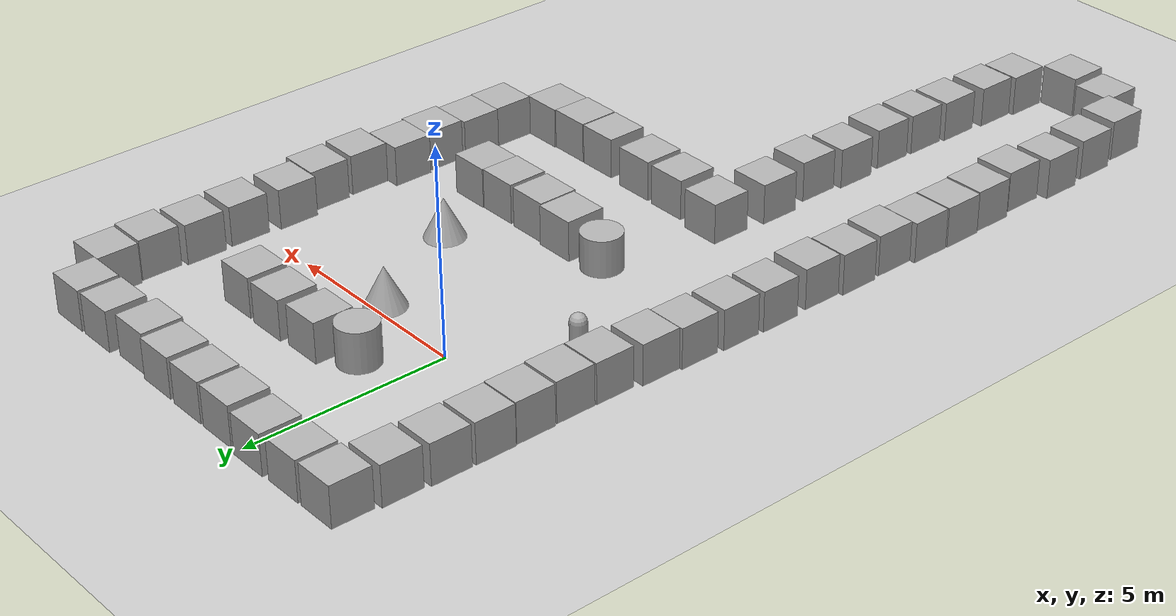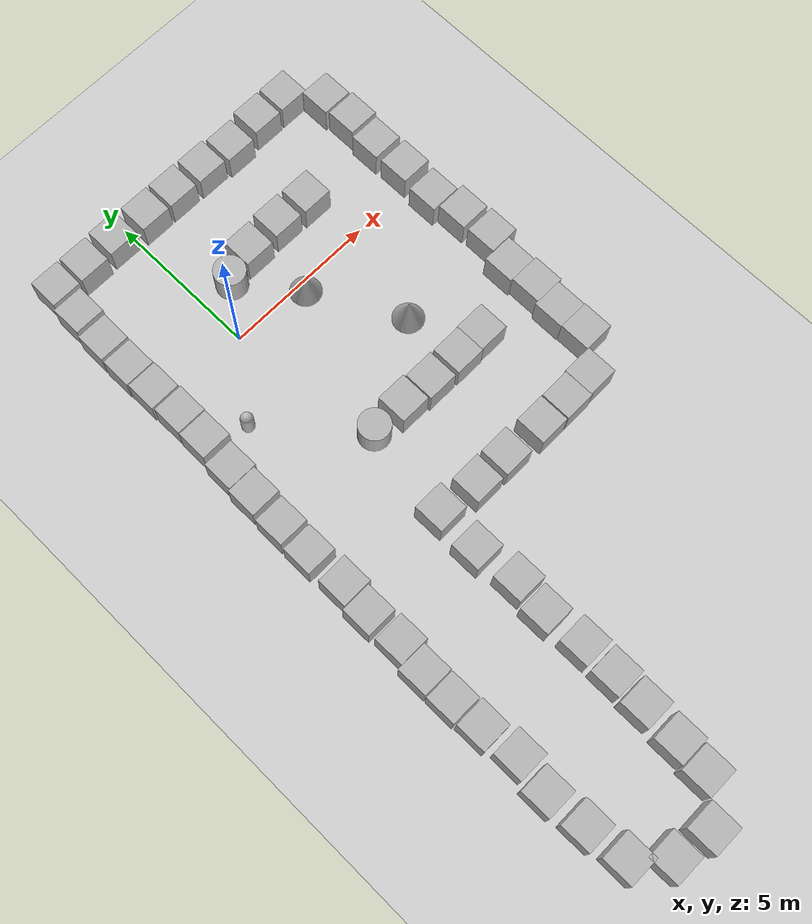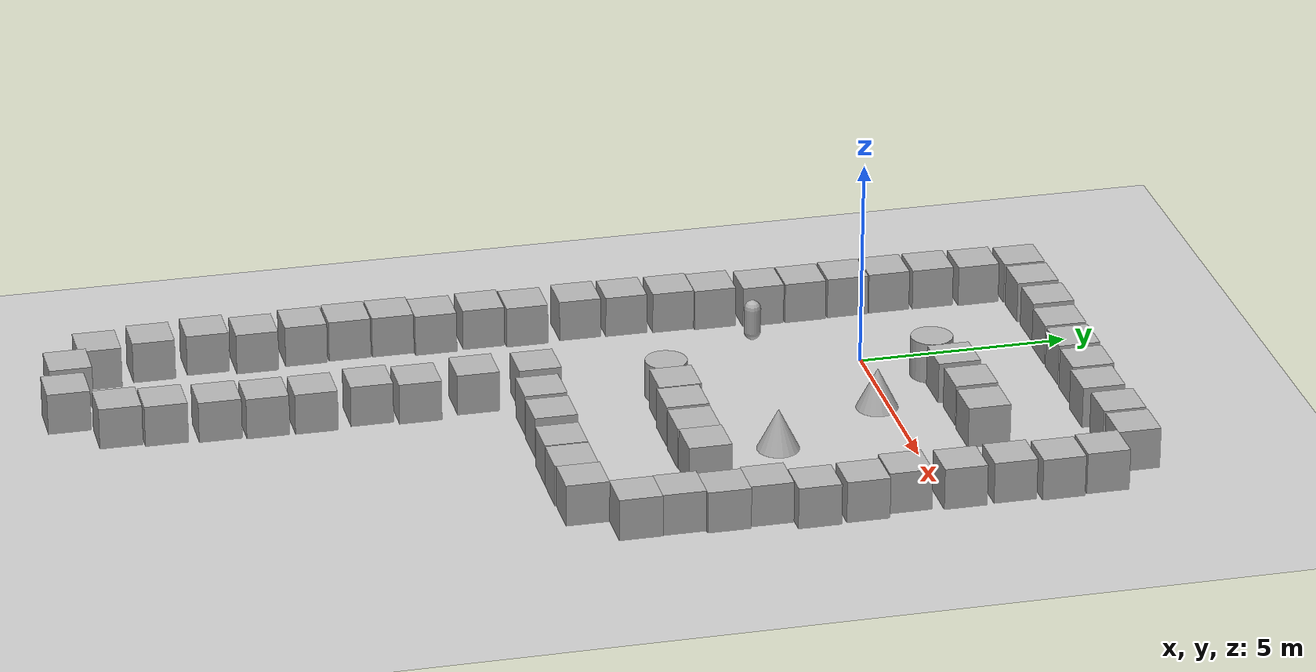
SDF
<sdf version='1.10'>
  <world name='empty'>
    <physics name='1ms' type='ignored'>
      <max_step_size>0.001</max_step_size>
      <real_time_factor>1</real_time_factor>
      <real_time_update_rate>1000</real_time_update_rate>
    </physics>
    <plugin name='gz::sim::systems::Physics' filename='gz-sim-physics-system'/>
    <plugin name='gz::sim::systems::UserCommands' filename='gz-sim-user-commands-system'/>
    <plugin name='gz::sim::systems::SceneBroadcaster' filename='gz-sim-scene-broadcaster-system'/>
    <plugin name='gz::sim::systems::Sensors' filename='gz-sim-sensors-system'>
      <render_engine>ogre2</render_engine>
    </plugin>
    <plugin name='gz::sim::systems::Contact' filename='gz-sim-contact-system'/>
    <gravity>0 0 -9.8000000000000007</gravity>
    <magnetic_field>5.5644999999999998e-06 2.2875799999999999e-05 -4.2388400000000002e-05</magnetic_field>
    <atmosphere type='adiabatic'/>
    <scene>
      <ambient>0.400000006 0.400000006 0.400000006 1</ambient>
      <background>0.699999988 0.699999988 0.699999988 1</background>
      <shadows>true</shadows>
    </scene>
    <model name='ground_plane'>
      <static>true</static>
      <link name='link'>
        <collision name='collision'>
          <geometry>
            <plane>
              <normal>0 0 1</normal>
              <size>100 100</size>
            </plane>
          </geometry>
          <surface>
            <friction>
              <ode/>
            </friction>
            <bounce/>
            <contact/>
          </surface>
        </collision>
        <visual name='visual'>
          <geometry>
            <plane>
              <normal>0 0 1</normal>
              <size>100 100</size>
            </plane>
          </geometry>
          <material>
            <ambient>0.800000012 0.800000012 0.800000012 1</ambient>
            <diffuse>0.800000012 0.800000012 0.800000012 1</diffuse>
            <specular>0.800000012 0.800000012 0.800000012 1</specular>
          </material>
        </visual>
        <pose>0 0 0 0 0 0</pose>
        <inertial>
          <pose>0 0 0 0 0 0</pose>
          <mass>1</mass>
          <inertia>
            <ixx>1</ixx>
            <ixy>0</ixy>
            <ixz>0</ixz>
            <iyy>1</iyy>
            <iyz>0</iyz>
            <izz>1</izz>
          </inertia>
        </inertial>
        <enable_wind>false</enable_wind>
      </link>
      <pose>0 0 0 0 0 0</pose>
      <self_collide>false</self_collide>
    </model>
    <model name='box'>
      <pose>1.8029219467110664 -4.9402323017846799 0.49999999970892495 1.9456243348768095e-21 -2.0287702973480091e-21 -7.5527752180039009e-22</pose>
      <link name='box_link'>
        <inertial>
          <inertia>
            <ixx>0.16666</ixx>
            <ixy>0</ixy>
            <ixz>0</ixz>
            <iyy>0.16666</iyy>
            <iyz>0</iyz>
            <izz>0.16666</izz>
          </inertia>
          <mass>1</mass>
          <pose>0 0 0 0 0 0</pose>
        </inertial>
        <collision name='box_collision'>
          <geometry>
            <box>
              <size>1 1 1</size>
            </box>
          </geometry>
          <surface>
            <friction>
              <ode/>
            </friction>
            <bounce/>
            <contact/>
          </surface>
        </collision>
        <visual name='box_visual'>
          <geometry>
            <box>
              <size>1 1 1</size>
            </box>
          </geometry>
          <material>
            <ambient>0.300000012 0.300000012 0.300000012 1</ambient>
            <diffuse>0.699999988 0.699999988 0.699999988 1</diffuse>
            <specular>1 1 1 1</specular>
          </material>
        </visual>
        <pose>0 0 0 0 0 0</pose>
        <enable_wind>false</enable_wind>
      </link>
      <static>false</static>
      <self_collide>false</self_collide>
    </model>
    <model name='cylinder'>
      <pose>0.69742500782012939 -4.8877110481262207 0.39216804054167947 1.731746546604768e-17 -2.62531762644311e-18 -3.2708537194835528e-19</pose>
      <link name='cylinder_link'>
        <inertial>
          <inertia>
            <ixx>0.14580000000000001</ixx>
            <ixy>0</ixy>
            <ixz>0</ixz>
            <iyy>0.14580000000000001</iyy>
            <iyz>0</iyz>
            <izz>0.125</izz>
          </inertia>
          <mass>1</mass>
          <pose>0 0 0 0 0 0</pose>
        </inertial>
        <collision name='cylinder_collision'>
          <geometry>
            <cylinder>
              <radius>0.5</radius>
              <length>1</length>
            </cylinder>
          </geometry>
          <surface>
            <friction>
              <ode/>
            </friction>
            <bounce/>
            <contact/>
          </surface>
        </collision>
        <visual name='cylinder_visual'>
          <geometry>
            <cylinder>
              <radius>0.5</radius>
              <length>1</length>
            </cylinder>
          </geometry>
          <material>
            <ambient>0.300000012 0.300000012 0.300000012 1</ambient>
            <diffuse>0.699999988 0.699999988 0.699999988 1</diffuse>
            <specular>1 1 1 1</specular>
          </material>
        </visual>
        <pose>0 0 0 0 0 0</pose>
        <enable_wind>false</enable_wind>
      </link>
      <static>false</static>
      <self_collide>false</self_collide>
    </model>
    <model name='box_0'>
      <pose>7.3041419982910156 2.606640100479126 0.49999999990199806 1.5168383847050144e-21 -6.8284900387290397e-21 -7.2088919212664049e-22</pose>
      <link name='box_link'>
        <inertial>
          <inertia>
            <ixx>0.16666</ixx>
            <ixy>0</ixy>
            <ixz>0</ixz>
            <iyy>0.16666</iyy>
            <iyz>0</iyz>
            <izz>0.16666</izz>
          </inertia>
          <mass>1</mass>
          <pose>0 0 0 0 0 0</pose>
        </inertial>
        <collision name='box_collision'>
          <geometry>
            <box>
              <size>1 1 1</size>
            </box>
          </geometry>
          <surface>
            <friction>
              <ode/>
            </friction>
            <bounce/>
            <contact/>
          </surface>
        </collision>
        <visual name='box_visual'>
          <geometry>
            <box>
              <size>1 1 1</size>
            </box>
          </geometry>
          <material>
            <ambient>0.300000012 0.300000012 0.300000012 1</ambient>
            <diffuse>0.699999988 0.699999988 0.699999988 1</diffuse>
            <specular>1 1 1 1</specular>
          </material>
        </visual>
        <pose>0 0 0 0 0 0</pose>
        <enable_wind>false</enable_wind>
      </link>
      <static>false</static>
      <self_collide>false</self_collide>
    </model>
    <model name='box_1'>
      <pose>7.2105679512023926 1.4994100332260132 0.49999999990199806 1.2287045058202266e-21 -2.8117306067242851e-21 -7.0165871101099256e-22</pose>
      <link name='box_link'>
        <inertial>
          <inertia>
            <ixx>0.16666</ixx>
            <ixy>0</ixy>
            <ixz>0</ixz>
            <iyy>0.16666</iyy>
            <iyz>0</iyz>
            <izz>0.16666</izz>
          </inertia>
          <mass>1</mass>
          <pose>0 0 0 0 0 0</pose>
        </inertial>
        <collision name='box_collision'>
          <geometry>
            <box>
              <size>1 1 1</size>
            </box>
          </geometry>
          <surface>
            <friction>
              <ode/>
            </friction>
            <bounce/>
            <contact/>
          </surface>
        </collision>
        <visual name='box_visual'>
          <geometry>
            <box>
              <size>1 1 1</size>
            </box>
          </geometry>
          <material>
            <ambient>0.300000012 0.300000012 0.300000012 1</ambient>
            <diffuse>0.699999988 0.699999988 0.699999988 1</diffuse>
            <specular>1 1 1 1</specular>
          </material>
        </visual>
        <pose>0 0 0 0 0 0</pose>
        <enable_wind>false</enable_wind>
      </link>
      <static>false</static>
      <self_collide>false</self_collide>
    </model>
    <model name='box_2'>
      <pose>7.2486476898193359 0.32666200399398804 0.49999999990199806 1.7912915900273766e-22 -3.8511324085270631e-21 -5.6253342361181017e-22</pose>
      <link name='box_link'>
        <inertial>
          <inertia>
            <ixx>0.16666</ixx>
            <ixy>0</ixy>
            <ixz>0</ixz>
            <iyy>0.16666</iyy>
            <iyz>0</iyz>
            <izz>0.16666</izz>
          </inertia>
          <mass>1</mass>
          <pose>0 0 0 0 0 0</pose>
        </inertial>
        <collision name='box_collision'>
          <geometry>
            <box>
              <size>1 1 1</size>
            </box>
          </geometry>
          <surface>
            <friction>
              <ode/>
            </friction>
            <bounce/>
            <contact/>
          </surface>
        </collision>
        <visual name='box_visual'>
          <geometry>
            <box>
              <size>1 1 1</size>
            </box>
          </geometry>
          <material>
            <ambient>0.300000012 0.300000012 0.300000012 1</ambient>
            <diffuse>0.699999988 0.699999988 0.699999988 1</diffuse>
            <specular>1 1 1 1</specular>
          </material>
        </visual>
        <pose>0 0 0 0 0 0</pose>
        <enable_wind>false</enable_wind>
      </link>
      <static>false</static>
      <self_collide>false</self_collide>
    </model>
    <model name='box_3'>
      <pose>2.837014502640967 -5.0088500809708263 0.49999999980497606 1.0048033485058014e-21 -2.4640853465547739e-21 -3.9210766489770922e-22</pose>
      <link name='box_link'>
        <inertial>
          <inertia>
            <ixx>0.16666</ixx>
            <ixy>0</ixy>
            <ixz>0</ixz>
            <iyy>0.16666</iyy>
            <iyz>0</iyz>
            <izz>0.16666</izz>
          </inertia>
          <mass>1</mass>
          <pose>0 0 0 0 0 0</pose>
        </inertial>
        <collision name='box_collision'>
          <geometry>
            <box>
              <size>1 1 1</size>
            </box>
          </geometry>
          <surface>
            <friction>
              <ode/>
            </friction>
            <bounce/>
            <contact/>
          </surface>
        </collision>
        <visual name='box_visual'>
          <geometry>
            <box>
              <size>1 1 1</size>
            </box>
          </geometry>
          <material>
            <ambient>0.300000012 0.300000012 0.300000012 1</ambient>
            <diffuse>0.699999988 0.699999988 0.699999988 1</diffuse>
            <specular>1 1 1 1</specular>
          </material>
        </visual>
        <pose>0 0 0 0 0 0</pose>
        <enable_wind>false</enable_wind>
      </link>
      <static>false</static>
      <self_collide>false</self_collide>
    </model>
    <model name='box_4'>
      <pose>3.9474809183531687 -5.0258722953265274 0.49999998529462536 3.7104125958135577e-09 -2.3067699219829278e-08 -3.0332183811339351e-07</pose>
      <link name='box_link'>
        <inertial>
          <inertia>
            <ixx>0.16666</ixx>
            <ixy>0</ixy>
            <ixz>0</ixz>
            <iyy>0.16666</iyy>
            <iyz>0</iyz>
            <izz>0.16666</izz>
          </inertia>
          <mass>1</mass>
          <pose>0 0 0 0 0 0</pose>
        </inertial>
        <collision name='box_collision'>
          <geometry>
            <box>
              <size>1 1 1</size>
            </box>
          </geometry>
          <surface>
            <friction>
              <ode/>
            </friction>
            <bounce/>
            <contact/>
          </surface>
        </collision>
        <visual name='box_visual'>
          <geometry>
            <box>
              <size>1 1 1</size>
            </box>
          </geometry>
          <material>
            <ambient>0.300000012 0.300000012 0.300000012 1</ambient>
            <diffuse>0.699999988 0.699999988 0.699999988 1</diffuse>
            <specular>1 1 1 1</specular>
          </material>
        </visual>
        <pose>0 0 0 0 0 0</pose>
        <enable_wind>false</enable_wind>
      </link>
      <static>false</static>
      <self_collide>false</self_collide>
    </model>
    <model name='box_5'>
      <pose>4.9474804862699848 -5.0026656346293397 0.49999998981609922 4.954454058698816e-11 1.2600079243989959e-08 -2.7732852854713343e-07</pose>
      <link name='box_link'>
        <inertial>
          <inertia>
            <ixx>0.16666</ixx>
            <ixy>0</ixy>
            <ixz>0</ixz>
            <iyy>0.16666</iyy>
            <iyz>0</iyz>
            <izz>0.16666</izz>
          </inertia>
          <mass>1</mass>
          <pose>0 0 0 0 0 0</pose>
        </inertial>
        <collision name='box_collision'>
          <geometry>
            <box>
              <size>1 1 1</size>
            </box>
          </geometry>
          <surface>
            <friction>
              <ode/>
            </friction>
            <bounce/>
            <contact/>
          </surface>
        </collision>
        <visual name='box_visual'>
          <geometry>
            <box>
              <size>1 1 1</size>
            </box>
          </geometry>
          <material>
            <ambient>0.300000012 0.300000012 0.300000012 1</ambient>
            <diffuse>0.699999988 0.699999988 0.699999988 1</diffuse>
            <specular>1 1 1 1</specular>
          </material>
        </visual>
        <pose>0 0 0 0 0 0</pose>
        <enable_wind>false</enable_wind>
      </link>
      <static>false</static>
      <self_collide>false</self_collide>
    </model>
    <model name='box_6'>
      <pose>7.1701793670654297 -0.93712598085403442 0.49999999990199806 2.8182951662427704e-21 -6.8739402334419064e-21 4.4936059007286857e-23</pose>
      <link name='box_link'>
        <inertial>
          <inertia>
            <ixx>0.16666</ixx>
            <ixy>0</ixy>
            <ixz>0</ixz>
            <iyy>0.16666</iyy>
            <iyz>0</iyz>
            <izz>0.16666</izz>
          </inertia>
          <mass>1</mass>
          <pose>0 0 0 0 0 0</pose>
        </inertial>
        <collision name='box_collision'>
          <geometry>
            <box>
              <size>1 1 1</size>
            </box>
          </geometry>
          <surface>
            <friction>
              <ode/>
            </friction>
            <bounce/>
            <contact/>
          </surface>
        </collision>
        <visual name='box_visual'>
          <geometry>
            <box>
              <size>1 1 1</size>
            </box>
          </geometry>
          <material>
            <ambient>0.300000012 0.300000012 0.300000012 1</ambient>
            <diffuse>0.699999988 0.699999988 0.699999988 1</diffuse>
            <specular>1 1 1 1</specular>
          </material>
        </visual>
        <pose>0 0 0 0 0 0</pose>
        <enable_wind>false</enable_wind>
      </link>
      <static>false</static>
      <self_collide>false</self_collide>
    </model>
    <model name='box_7'>
      <pose>7.3697552680969238 -1.9676200151443481 0.49999999990199806 8.7941230073099993e-22 -2.2139176495129975e-21 -3.6059947568603891e-22</pose>
      <link name='box_link'>
        <inertial>
          <inertia>
            <ixx>0.16666</ixx>
            <ixy>0</ixy>
            <ixz>0</ixz>
            <iyy>0.16666</iyy>
            <iyz>0</iyz>
            <izz>0.16666</izz>
          </inertia>
          <mass>1</mass>
          <pose>0 0 0 0 0 0</pose>
        </inertial>
        <collision name='box_collision'>
          <geometry>
            <box>
              <size>1 1 1</size>
            </box>
          </geometry>
          <surface>
            <friction>
              <ode/>
            </friction>
            <bounce/>
            <contact/>
          </surface>
        </collision>
        <visual name='box_visual'>
          <geometry>
            <box>
              <size>1 1 1</size>
            </box>
          </geometry>
          <material>
            <ambient>0.300000012 0.300000012 0.300000012 1</ambient>
            <diffuse>0.699999988 0.699999988 0.699999988 1</diffuse>
            <specular>1 1 1 1</specular>
          </material>
        </visual>
        <pose>0 0 0 0 0 0</pose>
        <enable_wind>false</enable_wind>
      </link>
      <static>false</static>
      <self_collide>false</self_collide>
    </model>
    <model name='box_8'>
      <pose>7.4158802936807593 -3.0975309045415642 0.49999999980497606 1.0048033485058014e-21 -2.4640853465547739e-21 -3.9210766489770922e-22</pose>
      <link name='box_link'>
        <inertial>
          <inertia>
            <ixx>0.16666</ixx>
            <ixy>0</ixy>
            <ixz>0</ixz>
            <iyy>0.16666</iyy>
            <iyz>0</iyz>
            <izz>0.16666</izz>
          </inertia>
          <mass>1</mass>
          <pose>0 0 0 0 0 0</pose>
        </inertial>
        <collision name='box_collision'>
          <geometry>
            <box>
              <size>1 1 1</size>
            </box>
          </geometry>
          <surface>
            <friction>
              <ode/>
            </friction>
            <bounce/>
            <contact/>
          </surface>
        </collision>
        <visual name='box_visual'>
          <geometry>
            <box>
              <size>1 1 1</size>
            </box>
          </geometry>
          <material>
            <ambient>0.300000012 0.300000012 0.300000012 1</ambient>
            <diffuse>0.699999988 0.699999988 0.699999988 1</diffuse>
            <specular>1 1 1 1</specular>
          </material>
        </visual>
        <pose>0 0 0 0 0 0</pose>
        <enable_wind>false</enable_wind>
      </link>
      <static>false</static>
      <self_collide>false</self_collide>
    </model>
    <model name='box_9'>
      <pose>7.083578917499171 -4.1148498478956697 0.4999999901998512 -5.0054462870855815e-09 6.7667792938227688e-13 -1.6027558188792147e-06</pose>
      <link name='box_link'>
        <inertial>
          <inertia>
            <ixx>0.16666</ixx>
            <ixy>0</ixy>
            <ixz>0</ixz>
            <iyy>0.16666</iyy>
            <iyz>0</iyz>
            <izz>0.16666</izz>
          </inertia>
          <mass>1</mass>
          <pose>0 0 0 0 0 0</pose>
        </inertial>
        <collision name='box_collision'>
          <geometry>
            <box>
              <size>1 1 1</size>
            </box>
          </geometry>
          <surface>
            <friction>
              <ode/>
            </friction>
            <bounce/>
            <contact/>
          </surface>
        </collision>
        <visual name='box_visual'>
          <geometry>
            <box>
              <size>1 1 1</size>
            </box>
          </geometry>
          <material>
            <ambient>0.300000012 0.300000012 0.300000012 1</ambient>
            <diffuse>0.699999988 0.699999988 0.699999988 1</diffuse>
            <specular>1 1 1 1</specular>
          </material>
        </visual>
        <pose>0 0 0 0 0 0</pose>
        <enable_wind>false</enable_wind>
      </link>
      <static>false</static>
      <self_collide>false</self_collide>
    </model>
    <model name='box_10'>
      <pose>7.157668728078316 -5.1148497796605223 0.49999999019985342 -5.0212384153694259e-09 6.604406486970901e-13 -1.5803644963507751e-06</pose>
      <link name='box_link'>
        <inertial>
          <inertia>
            <ixx>0.16666</ixx>
            <ixy>0</ixy>
            <ixz>0</ixz>
            <iyy>0.16666</iyy>
            <iyz>0</iyz>
            <izz>0.16666</izz>
          </inertia>
          <mass>1</mass>
          <pose>0 0 0 0 0 0</pose>
        </inertial>
        <collision name='box_collision'>
          <geometry>
            <box>
              <size>1 1 1</size>
            </box>
          </geometry>
          <surface>
            <friction>
              <ode/>
            </friction>
            <bounce/>
            <contact/>
          </surface>
        </collision>
        <visual name='box_visual'>
          <geometry>
            <box>
              <size>1 1 1</size>
            </box>
          </geometry>
          <material>
            <ambient>0.300000012 0.300000012 0.300000012 1</ambient>
            <diffuse>0.699999988 0.699999988 0.699999988 1</diffuse>
            <specular>1 1 1 1</specular>
          </material>
        </visual>
        <pose>0 0 0 0 0 0</pose>
        <enable_wind>false</enable_wind>
      </link>
      <static>false</static>
      <self_collide>false</self_collide>
    </model>
    <model name='box_11'>
      <pose>7.047095793072141 -6.1148499299846941 0.49999999020009811 -1.9531817952698124e-08 1.6817889764058319e-12 -1.0062951630002682e-06</pose>
      <link name='box_link'>
        <inertial>
          <inertia>
            <ixx>0.16666</ixx>
            <ixy>0</ixy>
            <ixz>0</ixz>
            <iyy>0.16666</iyy>
            <iyz>0</iyz>
            <izz>0.16666</izz>
          </inertia>
          <mass>1</mass>
          <pose>0 0 0 0 0 0</pose>
        </inertial>
        <collision name='box_collision'>
          <geometry>
            <box>
              <size>1 1 1</size>
            </box>
          </geometry>
          <surface>
            <friction>
              <ode/>
            </friction>
            <bounce/>
            <contact/>
          </surface>
        </collision>
        <visual name='box_visual'>
          <geometry>
            <box>
              <size>1 1 1</size>
            </box>
          </geometry>
          <material>
            <ambient>0.300000012 0.300000012 0.300000012 1</ambient>
            <diffuse>0.699999988 0.699999988 0.699999988 1</diffuse>
            <specular>1 1 1 1</specular>
          </material>
        </visual>
        <pose>0 0 0 0 0 0</pose>
        <enable_wind>false</enable_wind>
      </link>
      <static>false</static>
      <self_collide>false</self_collide>
    </model>
    <model name='box_12'>
      <pose>7.0684524366307429 -7.1148490083341205 0.4999999901984945 1.6116309610574025e-08 7.3847904851729951e-12 -1.7716566142746962e-06</pose>
      <link name='box_link'>
        <inertial>
          <inertia>
            <ixx>0.16666</ixx>
            <ixy>0</ixy>
            <ixz>0</ixz>
            <iyy>0.16666</iyy>
            <iyz>0</iyz>
            <izz>0.16666</izz>
          </inertia>
          <mass>1</mass>
          <pose>0 0 0 0 0 0</pose>
        </inertial>
        <collision name='box_collision'>
          <geometry>
            <box>
              <size>1 1 1</size>
            </box>
          </geometry>
          <surface>
            <friction>
              <ode/>
            </friction>
            <bounce/>
            <contact/>
          </surface>
        </collision>
        <visual name='box_visual'>
          <geometry>
            <box>
              <size>1 1 1</size>
            </box>
          </geometry>
          <material>
            <ambient>0.300000012 0.300000012 0.300000012 1</ambient>
            <diffuse>0.699999988 0.699999988 0.699999988 1</diffuse>
            <specular>1 1 1 1</specular>
          </material>
        </visual>
        <pose>0 0 0 0 0 0</pose>
        <enable_wind>false</enable_wind>
      </link>
      <static>false</static>
      <self_collide>false</self_collide>
    </model>
    <model name='box_13'>
      <pose>6.1244116256161005 -8.1146625602707871 0.49999999022078773 1.531830688740307e-08 4.4068036596287947e-09 -0.00041748080535213288</pose>
      <link name='box_link'>
        <inertial>
          <inertia>
            <ixx>0.16666</ixx>
            <ixy>0</ixy>
            <ixz>0</ixz>
            <iyy>0.16666</iyy>
            <iyz>0</iyz>
            <izz>0.16666</izz>
          </inertia>
          <mass>1</mass>
          <pose>0 0 0 0 0 0</pose>
        </inertial>
        <collision name='box_collision'>
          <geometry>
            <box>
              <size>1 1 1</size>
            </box>
          </geometry>
          <surface>
            <friction>
              <ode/>
            </friction>
            <bounce/>
            <contact/>
          </surface>
        </collision>
        <visual name='box_visual'>
          <geometry>
            <box>
              <size>1 1 1</size>
            </box>
          </geometry>
          <material>
            <ambient>0.300000012 0.300000012 0.300000012 1</ambient>
            <diffuse>0.699999988 0.699999988 0.699999988 1</diffuse>
            <specular>1 1 1 1</specular>
          </material>
        </visual>
        <pose>0 0 0 0 0 0</pose>
        <enable_wind>false</enable_wind>
      </link>
      <static>false</static>
      <self_collide>false</self_collide>
    </model>
    <model name='box_14'>
      <pose>5.1242039913273256 -8.1461779064023929 0.49999999019961472 6.9998158500655817e-13 -4.34922201743193e-09 -2.2626298584421248e-06</pose>
      <link name='box_link'>
        <inertial>
          <inertia>
            <ixx>0.16666</ixx>
            <ixy>0</ixy>
            <ixz>0</ixz>
            <iyy>0.16666</iyy>
            <iyz>0</iyz>
            <izz>0.16666</izz>
          </inertia>
          <mass>1</mass>
          <pose>0 0 0 0 0 0</pose>
        </inertial>
        <collision name='box_collision'>
          <geometry>
            <box>
              <size>1 1 1</size>
            </box>
          </geometry>
          <surface>
            <friction>
              <ode/>
            </friction>
            <bounce/>
            <contact/>
          </surface>
        </collision>
        <visual name='box_visual'>
          <geometry>
            <box>
              <size>1 1 1</size>
            </box>
          </geometry>
          <material>
            <ambient>0.300000012 0.300000012 0.300000012 1</ambient>
            <diffuse>0.699999988 0.699999988 0.699999988 1</diffuse>
            <specular>1 1 1 1</specular>
          </material>
        </visual>
        <pose>0 0 0 0 0 0</pose>
        <enable_wind>false</enable_wind>
      </link>
      <static>false</static>
      <self_collide>false</self_collide>
    </model>
    <model name='box_15'>
      <pose>4.0904389897101998 -8.1420347813360383 0.49999999980497606 1.0048033485058014e-21 -2.4640853465547739e-21 -3.9210766489770922e-22</pose>
      <link name='box_link'>
        <inertial>
          <inertia>
            <ixx>0.16666</ixx>
            <ixy>0</ixy>
            <ixz>0</ixz>
            <iyy>0.16666</iyy>
            <iyz>0</iyz>
            <izz>0.16666</izz>
          </inertia>
          <mass>1</mass>
          <pose>0 0 0 0 0 0</pose>
        </inertial>
        <collision name='box_collision'>
          <geometry>
            <box>
              <size>1 1 1</size>
            </box>
          </geometry>
          <surface>
            <friction>
              <ode/>
            </friction>
            <bounce/>
            <contact/>
          </surface>
        </collision>
        <visual name='box_visual'>
          <geometry>
            <box>
              <size>1 1 1</size>
            </box>
          </geometry>
          <material>
            <ambient>0.300000012 0.300000012 0.300000012 1</ambient>
            <diffuse>0.699999988 0.699999988 0.699999988 1</diffuse>
            <specular>1 1 1 1</specular>
          </material>
        </visual>
        <pose>0 0 0 0 0 0</pose>
        <enable_wind>false</enable_wind>
      </link>
      <static>false</static>
      <self_collide>false</self_collide>
    </model>
    <model name='box_16'>
      <pose>7.2284773836460516 3.6682880873089405 0.49999999019983887 1.7311705597020822e-08 5.0367547478796201e-13 2.2522522120258475e-06</pose>
      <link name='box_link'>
        <inertial>
          <inertia>
            <ixx>0.16666</ixx>
            <ixy>0</ixy>
            <ixz>0</ixz>
            <iyy>0.16666</iyy>
            <iyz>0</iyz>
            <izz>0.16666</izz>
          </inertia>
          <mass>1</mass>
          <pose>0 0 0 0 0 0</pose>
        </inertial>
        <collision name='box_collision'>
          <geometry>
            <box>
              <size>1 1 1</size>
            </box>
          </geometry>
          <surface>
            <friction>
              <ode/>
            </friction>
            <bounce/>
            <contact/>
          </surface>
        </collision>
        <visual name='box_visual'>
          <geometry>
            <box>
              <size>1 1 1</size>
            </box>
          </geometry>
          <material>
            <ambient>0.300000012 0.300000012 0.300000012 1</ambient>
            <diffuse>0.699999988 0.699999988 0.699999988 1</diffuse>
            <specular>1 1 1 1</specular>
          </material>
        </visual>
        <pose>0 0 0 0 0 0</pose>
        <enable_wind>false</enable_wind>
      </link>
      <static>false</static>
      <self_collide>false</self_collide>
    </model>
    <model name='box_17'>
      <pose>6.3534429665516008 4.6682840453196484 0.49999999019963143 -1.2765133758391765e-08 -2.2639738741085814e-13 3.4527045442701908e-06</pose>
      <link name='box_link'>
        <inertial>
          <inertia>
            <ixx>0.16666</ixx>
            <ixy>0</ixy>
            <ixz>0</ixz>
            <iyy>0.16666</iyy>
            <iyz>0</iyz>
            <izz>0.16666</izz>
          </inertia>
          <mass>1</mass>
          <pose>0 0 0 0 0 0</pose>
        </inertial>
        <collision name='box_collision'>
          <geometry>
            <box>
              <size>1 1 1</size>
            </box>
          </geometry>
          <surface>
            <friction>
              <ode/>
            </friction>
            <bounce/>
            <contact/>
          </surface>
        </collision>
        <visual name='box_visual'>
          <geometry>
            <box>
              <size>1 1 1</size>
            </box>
          </geometry>
          <material>
            <ambient>0.300000012 0.300000012 0.300000012 1</ambient>
            <diffuse>0.699999988 0.699999988 0.699999988 1</diffuse>
            <specular>1 1 1 1</specular>
          </material>
        </visual>
        <pose>0 0 0 0 0 0</pose>
        <enable_wind>false</enable_wind>
      </link>
      <static>false</static>
      <self_collide>false</self_collide>
    </model>
    <model name='box_18'>
      <pose>5.2534054060505504 4.6579889603353957 0.49999999990199806 6.2287739151293738e-22 9.3279666454713669e-22 -3.6315533669320137e-22</pose>
      <link name='box_link'>
        <inertial>
          <inertia>
            <ixx>0.16666</ixx>
            <ixy>0</ixy>
            <ixz>0</ixz>
            <iyy>0.16666</iyy>
            <iyz>0</iyz>
            <izz>0.16666</izz>
          </inertia>
          <mass>1</mass>
          <pose>0 0 0 0 0 0</pose>
        </inertial>
        <collision name='box_collision'>
          <geometry>
            <box>
              <size>1 1 1</size>
            </box>
          </geometry>
          <surface>
            <friction>
              <ode/>
            </friction>
            <bounce/>
            <contact/>
          </surface>
        </collision>
        <visual name='box_visual'>
          <geometry>
            <box>
              <size>1 1 1</size>
            </box>
          </geometry>
          <material>
            <ambient>0.300000012 0.300000012 0.300000012 1</ambient>
            <diffuse>0.699999988 0.699999988 0.699999988 1</diffuse>
            <specular>1 1 1 1</specular>
          </material>
        </visual>
        <pose>0 0 0 0 0 0</pose>
        <enable_wind>false</enable_wind>
      </link>
      <static>false</static>
      <self_collide>false</self_collide>
    </model>
    <model name='box_19'>
      <pose>4.0295776346560093 4.5452057706611155 0.49999999990199806 6.2287739151293738e-22 9.3279666454713669e-22 -3.6315533669320137e-22</pose>
      <link name='box_link'>
        <inertial>
          <inertia>
            <ixx>0.16666</ixx>
            <ixy>0</ixy>
            <ixz>0</ixz>
            <iyy>0.16666</iyy>
            <iyz>0</iyz>
            <izz>0.16666</izz>
          </inertia>
          <mass>1</mass>
          <pose>0 0 0 0 0 0</pose>
        </inertial>
        <collision name='box_collision'>
          <geometry>
            <box>
              <size>1 1 1</size>
            </box>
          </geometry>
          <surface>
            <friction>
              <ode/>
            </friction>
            <bounce/>
            <contact/>
          </surface>
        </collision>
        <visual name='box_visual'>
          <geometry>
            <box>
              <size>1 1 1</size>
            </box>
          </geometry>
          <material>
            <ambient>0.300000012 0.300000012 0.300000012 1</ambient>
            <diffuse>0.699999988 0.699999988 0.699999988 1</diffuse>
            <specular>1 1 1 1</specular>
          </material>
        </visual>
        <pose>0 0 0 0 0 0</pose>
        <enable_wind>false</enable_wind>
      </link>
      <static>false</static>
      <self_collide>false</self_collide>
    </model>
    <model name='box_20'>
      <pose>2.9275956714733198 4.6291333544808468 0.49999999990199806 6.2287739151293738e-22 9.3279666454713669e-22 -3.6315533669320137e-22</pose>
      <link name='box_link'>
        <inertial>
          <inertia>
            <ixx>0.16666</ixx>
            <ixy>0</ixy>
            <ixz>0</ixz>
            <iyy>0.16666</iyy>
            <iyz>0</iyz>
            <izz>0.16666</izz>
          </inertia>
          <mass>1</mass>
          <pose>0 0 0 0 0 0</pose>
        </inertial>
        <collision name='box_collision'>
          <geometry>
            <box>
              <size>1 1 1</size>
            </box>
          </geometry>
          <surface>
            <friction>
              <ode/>
            </friction>
            <bounce/>
            <contact/>
          </surface>
        </collision>
        <visual name='box_visual'>
          <geometry>
            <box>
              <size>1 1 1</size>
            </box>
          </geometry>
          <material>
            <ambient>0.300000012 0.300000012 0.300000012 1</ambient>
            <diffuse>0.699999988 0.699999988 0.699999988 1</diffuse>
            <specular>1 1 1 1</specular>
          </material>
        </visual>
        <pose>0 0 0 0 0 0</pose>
        <enable_wind>false</enable_wind>
      </link>
      <static>false</static>
      <self_collide>false</self_collide>
    </model>
    <model name='box_21'>
      <pose>1.7741337268243713 4.6472916629790317 0.49999999990199806 6.2287739151293738e-22 9.3279666454713669e-22 -3.6315533669320137e-22</pose>
      <link name='box_link'>
        <inertial>
          <inertia>
            <ixx>0.16666</ixx>
            <ixy>0</ixy>
            <ixz>0</ixz>
            <iyy>0.16666</iyy>
            <iyz>0</iyz>
            <izz>0.16666</izz>
          </inertia>
          <mass>1</mass>
          <pose>0 0 0 0 0 0</pose>
        </inertial>
        <collision name='box_collision'>
          <geometry>
            <box>
              <size>1 1 1</size>
            </box>
          </geometry>
          <surface>
            <friction>
              <ode/>
            </friction>
            <bounce/>
            <contact/>
          </surface>
        </collision>
        <visual name='box_visual'>
          <geometry>
            <box>
              <size>1 1 1</size>
            </box>
          </geometry>
          <material>
            <ambient>0.300000012 0.300000012 0.300000012 1</ambient>
            <diffuse>0.699999988 0.699999988 0.699999988 1</diffuse>
            <specular>1 1 1 1</specular>
          </material>
        </visual>
        <pose>0 0 0 0 0 0</pose>
        <enable_wind>false</enable_wind>
      </link>
      <static>false</static>
      <self_collide>false</self_collide>
    </model>
    <model name='box_22'>
      <pose>0.67671356024645357 4.6495231021759968 0.49999999990199806 6.2287739151293738e-22 9.3279666454713669e-22 -3.6315533669320137e-22</pose>
      <link name='box_link'>
        <inertial>
          <inertia>
            <ixx>0.16666</ixx>
            <ixy>0</ixy>
            <ixz>0</ixz>
            <iyy>0.16666</iyy>
            <iyz>0</iyz>
            <izz>0.16666</izz>
          </inertia>
          <mass>1</mass>
          <pose>0 0 0 0 0 0</pose>
        </inertial>
        <collision name='box_collision'>
          <geometry>
            <box>
              <size>1 1 1</size>
            </box>
          </geometry>
          <surface>
            <friction>
              <ode/>
            </friction>
            <bounce/>
            <contact/>
          </surface>
        </collision>
        <visual name='box_visual'>
          <geometry>
            <box>
              <size>1 1 1</size>
            </box>
          </geometry>
          <material>
            <ambient>0.300000012 0.300000012 0.300000012 1</ambient>
            <diffuse>0.699999988 0.699999988 0.699999988 1</diffuse>
            <specular>1 1 1 1</specular>
          </material>
        </visual>
        <pose>0 0 0 0 0 0</pose>
        <enable_wind>false</enable_wind>
      </link>
      <static>false</static>
      <self_collide>false</self_collide>
    </model>
    <model name='box_23'>
      <pose>-0.52900487386500306 4.7230642957541882 0.49999999990199806 6.2287739151293738e-22 9.3279666454713669e-22 -3.6315533669320137e-22</pose>
      <link name='box_link'>
        <inertial>
          <inertia>
            <ixx>0.16666</ixx>
            <ixy>0</ixy>
            <ixz>0</ixz>
            <iyy>0.16666</iyy>
            <iyz>0</iyz>
            <izz>0.16666</izz>
          </inertia>
          <mass>1</mass>
          <pose>0 0 0 0 0 0</pose>
        </inertial>
        <collision name='box_collision'>
          <geometry>
            <box>
              <size>1 1 1</size>
            </box>
          </geometry>
          <surface>
            <friction>
              <ode/>
            </friction>
            <bounce/>
            <contact/>
          </surface>
        </collision>
        <visual name='box_visual'>
          <geometry>
            <box>
              <size>1 1 1</size>
            </box>
          </geometry>
          <material>
            <ambient>0.300000012 0.300000012 0.300000012 1</ambient>
            <diffuse>0.699999988 0.699999988 0.699999988 1</diffuse>
            <specular>1 1 1 1</specular>
          </material>
        </visual>
        <pose>0 0 0 0 0 0</pose>
        <enable_wind>false</enable_wind>
      </link>
      <static>false</static>
      <self_collide>false</self_collide>
    </model>
    <model name='box_24'>
      <pose>-1.6940723823211039 4.6902858663462901 0.49999999990199806 6.2287739151293738e-22 9.3279666454713669e-22 -3.6315533669320137e-22</pose>
      <link name='box_link'>
        <inertial>
          <inertia>
            <ixx>0.16666</ixx>
            <ixy>0</ixy>
            <ixz>0</ixz>
            <iyy>0.16666</iyy>
            <iyz>0</iyz>
            <izz>0.16666</izz>
          </inertia>
          <mass>1</mass>
          <pose>0 0 0 0 0 0</pose>
        </inertial>
        <collision name='box_collision'>
          <geometry>
            <box>
              <size>1 1 1</size>
            </box>
          </geometry>
          <surface>
            <friction>
              <ode/>
            </friction>
            <bounce/>
            <contact/>
          </surface>
        </collision>
        <visual name='box_visual'>
          <geometry>
            <box>
              <size>1 1 1</size>
            </box>
          </geometry>
          <material>
            <ambient>0.300000012 0.300000012 0.300000012 1</ambient>
            <diffuse>0.699999988 0.699999988 0.699999988 1</diffuse>
            <specular>1 1 1 1</specular>
          </material>
        </visual>
        <pose>0 0 0 0 0 0</pose>
        <enable_wind>false</enable_wind>
      </link>
      <static>false</static>
      <self_collide>false</self_collide>
    </model>
    <model name='box_25'>
      <pose>-2.7844191484214762 4.680301058964357 0.49999999990199806 6.2287739151293738e-22 9.3279666454713669e-22 -3.6315533669320137e-22</pose>
      <link name='box_link'>
        <inertial>
          <inertia>
            <ixx>0.16666</ixx>
            <ixy>0</ixy>
            <ixz>0</ixz>
            <iyy>0.16666</iyy>
            <iyz>0</iyz>
            <izz>0.16666</izz>
          </inertia>
          <mass>1</mass>
          <pose>0 0 0 0 0 0</pose>
        </inertial>
        <collision name='box_collision'>
          <geometry>
            <box>
              <size>1 1 1</size>
            </box>
          </geometry>
          <surface>
            <friction>
              <ode/>
            </friction>
            <bounce/>
            <contact/>
          </surface>
        </collision>
        <visual name='box_visual'>
          <geometry>
            <box>
              <size>1 1 1</size>
            </box>
          </geometry>
          <material>
            <ambient>0.300000012 0.300000012 0.300000012 1</ambient>
            <diffuse>0.699999988 0.699999988 0.699999988 1</diffuse>
            <specular>1 1 1 1</specular>
          </material>
        </visual>
        <pose>0 0 0 0 0 0</pose>
        <enable_wind>false</enable_wind>
      </link>
      <static>false</static>
      <self_collide>false</self_collide>
    </model>
    <model name='box_26'>
      <pose>-2.8712853102488949 3.5696913958604108 0.49999999990199806 6.2287739151293738e-22 9.3279666454713669e-22 -3.6315533669320137e-22</pose>
      <link name='box_link'>
        <inertial>
          <inertia>
            <ixx>0.16666</ixx>
            <ixy>0</ixy>
            <ixz>0</ixz>
            <iyy>0.16666</iyy>
            <iyz>0</iyz>
            <izz>0.16666</izz>
          </inertia>
          <mass>1</mass>
          <pose>0 0 0 0 0 0</pose>
        </inertial>
        <collision name='box_collision'>
          <geometry>
            <box>
              <size>1 1 1</size>
            </box>
          </geometry>
          <surface>
            <friction>
              <ode/>
            </friction>
            <bounce/>
            <contact/>
          </surface>
        </collision>
        <visual name='box_visual'>
          <geometry>
            <box>
              <size>1 1 1</size>
            </box>
          </geometry>
          <material>
            <ambient>0.300000012 0.300000012 0.300000012 1</ambient>
            <diffuse>0.699999988 0.699999988 0.699999988 1</diffuse>
            <specular>1 1 1 1</specular>
          </material>
        </visual>
        <pose>0 0 0 0 0 0</pose>
        <enable_wind>false</enable_wind>
      </link>
      <static>false</static>
      <self_collide>false</self_collide>
    </model>
    <model name='box_27'>
      <pose>-2.9324519904683397 2.4445221172465974 0.49999999990199806 6.2287739151293738e-22 9.3279666454713669e-22 -3.6315533669320137e-22</pose>
      <link name='box_link'>
        <inertial>
          <inertia>
            <ixx>0.16666</ixx>
            <ixy>0</ixy>
            <ixz>0</ixz>
            <iyy>0.16666</iyy>
            <iyz>0</iyz>
            <izz>0.16666</izz>
          </inertia>
          <mass>1</mass>
          <pose>0 0 0 0 0 0</pose>
        </inertial>
        <collision name='box_collision'>
          <geometry>
            <box>
              <size>1 1 1</size>
            </box>
          </geometry>
          <surface>
            <friction>
              <ode/>
            </friction>
            <bounce/>
            <contact/>
          </surface>
        </collision>
        <visual name='box_visual'>
          <geometry>
            <box>
              <size>1 1 1</size>
            </box>
          </geometry>
          <material>
            <ambient>0.300000012 0.300000012 0.300000012 1</ambient>
            <diffuse>0.699999988 0.699999988 0.699999988 1</diffuse>
            <specular>1 1 1 1</specular>
          </material>
        </visual>
        <pose>0 0 0 0 0 0</pose>
        <enable_wind>false</enable_wind>
      </link>
      <static>false</static>
      <self_collide>false</self_collide>
    </model>
    <model name='box_28'>
      <pose>-2.9430180161721049 1.361581606022769 0.49999999990199806 6.2287739151293738e-22 9.3279666454713669e-22 -3.6315533669320137e-22</pose>
      <link name='box_link'>
        <inertial>
          <inertia>
            <ixx>0.16666</ixx>
            <ixy>0</ixy>
            <ixz>0</ixz>
            <iyy>0.16666</iyy>
            <iyz>0</iyz>
            <izz>0.16666</izz>
          </inertia>
          <mass>1</mass>
          <pose>0 0 0 0 0 0</pose>
        </inertial>
        <collision name='box_collision'>
          <geometry>
            <box>
              <size>1 1 1</size>
            </box>
          </geometry>
          <surface>
            <friction>
              <ode/>
            </friction>
            <bounce/>
            <contact/>
          </surface>
        </collision>
        <visual name='box_visual'>
          <geometry>
            <box>
              <size>1 1 1</size>
            </box>
          </geometry>
          <material>
            <ambient>0.300000012 0.300000012 0.300000012 1</ambient>
            <diffuse>0.699999988 0.699999988 0.699999988 1</diffuse>
            <specular>1 1 1 1</specular>
          </material>
        </visual>
        <pose>0 0 0 0 0 0</pose>
        <enable_wind>false</enable_wind>
      </link>
      <static>false</static>
      <self_collide>false</self_collide>
    </model>
    <model name='box_29'>
      <pose>-2.9187763636575417 0.33238052469198842 0.49999999990199806 6.2287739151293738e-22 9.3279666454713669e-22 -3.6315533669320137e-22</pose>
      <link name='box_link'>
        <inertial>
          <inertia>
            <ixx>0.16666</ixx>
            <ixy>0</ixy>
            <ixz>0</ixz>
            <iyy>0.16666</iyy>
            <iyz>0</iyz>
            <izz>0.16666</izz>
          </inertia>
          <mass>1</mass>
          <pose>0 0 0 0 0 0</pose>
        </inertial>
        <collision name='box_collision'>
          <geometry>
            <box>
              <size>1 1 1</size>
            </box>
          </geometry>
          <surface>
            <friction>
              <ode/>
            </friction>
            <bounce/>
            <contact/>
          </surface>
        </collision>
        <visual name='box_visual'>
          <geometry>
            <box>
              <size>1 1 1</size>
            </box>
          </geometry>
          <material>
            <ambient>0.300000012 0.300000012 0.300000012 1</ambient>
            <diffuse>0.699999988 0.699999988 0.699999988 1</diffuse>
            <specular>1 1 1 1</specular>
          </material>
        </visual>
        <pose>0 0 0 0 0 0</pose>
        <enable_wind>false</enable_wind>
      </link>
      <static>false</static>
      <self_collide>false</self_collide>
    </model>
    <model name='box_30'>
      <pose>-2.8841041433069523 -0.72282486379328414 0.49999999990199806 6.2287739151293738e-22 9.3279666454713669e-22 -3.6315533669320137e-22</pose>
      <link name='box_link'>
        <inertial>
          <inertia>
            <ixx>0.16666</ixx>
            <ixy>0</ixy>
            <ixz>0</ixz>
            <iyy>0.16666</iyy>
            <iyz>0</iyz>
            <izz>0.16666</izz>
          </inertia>
          <mass>1</mass>
          <pose>0 0 0 0 0 0</pose>
        </inertial>
        <collision name='box_collision'>
          <geometry>
            <box>
              <size>1 1 1</size>
            </box>
          </geometry>
          <surface>
            <friction>
              <ode/>
            </friction>
            <bounce/>
            <contact/>
          </surface>
        </collision>
        <visual name='box_visual'>
          <geometry>
            <box>
              <size>1 1 1</size>
            </box>
          </geometry>
          <material>
            <ambient>0.300000012 0.300000012 0.300000012 1</ambient>
            <diffuse>0.699999988 0.699999988 0.699999988 1</diffuse>
            <specular>1 1 1 1</specular>
          </material>
        </visual>
        <pose>0 0 0 0 0 0</pose>
        <enable_wind>false</enable_wind>
      </link>
      <static>false</static>
      <self_collide>false</self_collide>
    </model>
    <model name='box_31'>
      <pose>-2.8944062708120146 -1.7570096625936276 0.49999999990199806 6.2287739151293738e-22 9.3279666454713669e-22 -3.6315533669320137e-22</pose>
      <link name='box_link'>
        <inertial>
          <inertia>
            <ixx>0.16666</ixx>
            <ixy>0</ixy>
            <ixz>0</ixz>
            <iyy>0.16666</iyy>
            <iyz>0</iyz>
            <izz>0.16666</izz>
          </inertia>
          <mass>1</mass>
          <pose>0 0 0 0 0 0</pose>
        </inertial>
        <collision name='box_collision'>
          <geometry>
            <box>
              <size>1 1 1</size>
            </box>
          </geometry>
          <surface>
            <friction>
              <ode/>
            </friction>
            <bounce/>
            <contact/>
          </surface>
        </collision>
        <visual name='box_visual'>
          <geometry>
            <box>
              <size>1 1 1</size>
            </box>
          </geometry>
          <material>
            <ambient>0.300000012 0.300000012 0.300000012 1</ambient>
            <diffuse>0.699999988 0.699999988 0.699999988 1</diffuse>
            <specular>1 1 1 1</specular>
          </material>
        </visual>
        <pose>0 0 0 0 0 0</pose>
        <enable_wind>false</enable_wind>
      </link>
      <static>false</static>
      <self_collide>false</self_collide>
    </model>
    <model name='box_32'>
      <pose>-2.996549854148201 -2.9150881569977187 0.49999999990199806 6.2287739151293738e-22 9.3279666454713669e-22 -3.6315533669320137e-22</pose>
      <link name='box_link'>
        <inertial>
          <inertia>
            <ixx>0.16666</ixx>
            <ixy>0</ixy>
            <ixz>0</ixz>
            <iyy>0.16666</iyy>
            <iyz>0</iyz>
            <izz>0.16666</izz>
          </inertia>
          <mass>1</mass>
          <pose>0 0 0 0 0 0</pose>
        </inertial>
        <collision name='box_collision'>
          <geometry>
            <box>
              <size>1 1 1</size>
            </box>
          </geometry>
          <surface>
            <friction>
              <ode/>
            </friction>
            <bounce/>
            <contact/>
          </surface>
        </collision>
        <visual name='box_visual'>
          <geometry>
            <box>
              <size>1 1 1</size>
            </box>
          </geometry>
          <material>
            <ambient>0.300000012 0.300000012 0.300000012 1</ambient>
            <diffuse>0.699999988 0.699999988 0.699999988 1</diffuse>
            <specular>1 1 1 1</specular>
          </material>
        </visual>
        <pose>0 0 0 0 0 0</pose>
        <enable_wind>false</enable_wind>
      </link>
      <static>false</static>
      <self_collide>false</self_collide>
    </model>
    <model name='box_33'>
      <pose>-3.0658264451040367 -3.9244253724440612 0.49999999990199806 -4.9431071861903433e-22 9.8960145325785522e-22 1.6714802379934959e-22</pose>
      <link name='box_link'>
        <inertial>
          <inertia>
            <ixx>0.16666</ixx>
            <ixy>0</ixy>
            <ixz>0</ixz>
            <iyy>0.16666</iyy>
            <iyz>0</iyz>
            <izz>0.16666</izz>
          </inertia>
          <mass>1</mass>
          <pose>0 0 0 0 0 0</pose>
        </inertial>
        <collision name='box_collision'>
          <geometry>
            <box>
              <size>1 1 1</size>
            </box>
          </geometry>
          <surface>
            <friction>
              <ode/>
            </friction>
            <bounce/>
            <contact/>
          </surface>
        </collision>
        <visual name='box_visual'>
          <geometry>
            <box>
              <size>1 1 1</size>
            </box>
          </geometry>
          <material>
            <ambient>0.300000012 0.300000012 0.300000012 1</ambient>
            <diffuse>0.699999988 0.699999988 0.699999988 1</diffuse>
            <specular>1 1 1 1</specular>
          </material>
        </visual>
        <pose>0 0 0 0 0 0</pose>
        <enable_wind>false</enable_wind>
      </link>
      <static>false</static>
      <self_collide>false</self_collide>
    </model>
    <model name='box_34'>
      <pose>-3.1076568110748073 -5.0616794321280825 0.49999999990199806 6.2287739151293738e-22 9.3279666454713669e-22 -3.6315533669320137e-22</pose>
      <link name='box_link'>
        <inertial>
          <inertia>
            <ixx>0.16666</ixx>
            <ixy>0</ixy>
            <ixz>0</ixz>
            <iyy>0.16666</iyy>
            <iyz>0</iyz>
            <izz>0.16666</izz>
          </inertia>
          <mass>1</mass>
          <pose>0 0 0 0 0 0</pose>
        </inertial>
        <collision name='box_collision'>
          <geometry>
            <box>
              <size>1 1 1</size>
            </box>
          </geometry>
          <surface>
            <friction>
              <ode/>
            </friction>
            <bounce/>
            <contact/>
          </surface>
        </collision>
        <visual name='box_visual'>
          <geometry>
            <box>
              <size>1 1 1</size>
            </box>
          </geometry>
          <material>
            <ambient>0.300000012 0.300000012 0.300000012 1</ambient>
            <diffuse>0.699999988 0.699999988 0.699999988 1</diffuse>
            <specular>1 1 1 1</specular>
          </material>
        </visual>
        <pose>0 0 0 0 0 0</pose>
        <enable_wind>false</enable_wind>
      </link>
      <static>false</static>
      <self_collide>false</self_collide>
    </model>
    <model name='box_35'>
      <pose>0.24766042885596473 -7.8956005604393997 0.49999999990199806 6.2287739151293738e-22 9.3279666454713669e-22 -3.6315533669320137e-22</pose>
      <link name='box_link'>
        <inertial>
          <inertia>
            <ixx>0.16666</ixx>
            <ixy>0</ixy>
            <ixz>0</ixz>
            <iyy>0.16666</iyy>
            <iyz>0</iyz>
            <izz>0.16666</izz>
          </inertia>
          <mass>1</mass>
          <pose>0 0 0 0 0 0</pose>
        </inertial>
        <collision name='box_collision'>
          <geometry>
            <box>
              <size>1 1 1</size>
            </box>
          </geometry>
          <surface>
            <friction>
              <ode/>
            </friction>
            <bounce/>
            <contact/>
          </surface>
        </collision>
        <visual name='box_visual'>
          <geometry>
            <box>
              <size>1 1 1</size>
            </box>
          </geometry>
          <material>
            <ambient>0.300000012 0.300000012 0.300000012 1</ambient>
            <diffuse>0.699999988 0.699999988 0.699999988 1</diffuse>
            <specular>1 1 1 1</specular>
          </material>
        </visual>
        <pose>0 0 0 0 0 0</pose>
        <enable_wind>false</enable_wind>
      </link>
      <static>false</static>
      <self_collide>false</self_collide>
    </model>
    <model name='box_36'>
      <pose>0.33365914200646607 -10.742962308740333 0.49999999990199806 6.2287739151293738e-22 9.3279666454713669e-22 -3.6315533669320137e-22</pose>
      <link name='box_link'>
        <inertial>
          <inertia>
            <ixx>0.16666</ixx>
            <ixy>0</ixy>
            <ixz>0</ixz>
            <iyy>0.16666</iyy>
            <iyz>0</iyz>
            <izz>0.16666</izz>
          </inertia>
          <mass>1</mass>
          <pose>0 0 0 0 0 0</pose>
        </inertial>
        <collision name='box_collision'>
          <geometry>
            <box>
              <size>1 1 1</size>
            </box>
          </geometry>
          <surface>
            <friction>
              <ode/>
            </friction>
            <bounce/>
            <contact/>
          </surface>
        </collision>
        <visual name='box_visual'>
          <geometry>
            <box>
              <size>1 1 1</size>
            </box>
          </geometry>
          <material>
            <ambient>0.300000012 0.300000012 0.300000012 1</ambient>
            <diffuse>0.699999988 0.699999988 0.699999988 1</diffuse>
            <specular>1 1 1 1</specular>
          </material>
        </visual>
        <pose>0 0 0 0 0 0</pose>
        <enable_wind>false</enable_wind>
      </link>
      <static>false</static>
      <self_collide>false</self_collide>
    </model>
    <model name='box_37'>
      <pose>2.7086985949157238 -8.0697046981979508 0.49999999990199806 6.2287739151293738e-22 9.3279666454713669e-22 -3.6315533669320137e-22</pose>
      <link name='box_link'>
        <inertial>
          <inertia>
            <ixx>0.16666</ixx>
            <ixy>0</ixy>
            <ixz>0</ixz>
            <iyy>0.16666</iyy>
            <iyz>0</iyz>
            <izz>0.16666</izz>
          </inertia>
          <mass>1</mass>
          <pose>0 0 0 0 0 0</pose>
        </inertial>
        <collision name='box_collision'>
          <geometry>
            <box>
              <size>1 1 1</size>
            </box>
          </geometry>
          <surface>
            <friction>
              <ode/>
            </friction>
            <bounce/>
            <contact/>
          </surface>
        </collision>
        <visual name='box_visual'>
          <geometry>
            <box>
              <size>1 1 1</size>
            </box>
          </geometry>
          <material>
            <ambient>0.300000012 0.300000012 0.300000012 1</ambient>
            <diffuse>0.699999988 0.699999988 0.699999988 1</diffuse>
            <specular>1 1 1 1</specular>
          </material>
        </visual>
        <pose>0 0 0 0 0 0</pose>
        <enable_wind>false</enable_wind>
      </link>
      <static>false</static>
      <self_collide>false</self_collide>
    </model>
    <model name='box_38'>
      <pose>1.558771340348704 -8.0505541174595496 0.49999999990199806 6.2287739151293738e-22 9.3279666454713669e-22 -3.6315533669320137e-22</pose>
      <link name='box_link'>
        <inertial>
          <inertia>
            <ixx>0.16666</ixx>
            <ixy>0</ixy>
            <ixz>0</ixz>
            <iyy>0.16666</iyy>
            <iyz>0</iyz>
            <izz>0.16666</izz>
          </inertia>
          <mass>1</mass>
          <pose>0 0 0 0 0 0</pose>
        </inertial>
        <collision name='box_collision'>
          <geometry>
            <box>
              <size>1 1 1</size>
            </box>
          </geometry>
          <surface>
            <friction>
              <ode/>
            </friction>
            <bounce/>
            <contact/>
          </surface>
        </collision>
        <visual name='box_visual'>
          <geometry>
            <box>
              <size>1 1 1</size>
            </box>
          </geometry>
          <material>
            <ambient>0.300000012 0.300000012 0.300000012 1</ambient>
            <diffuse>0.699999988 0.699999988 0.699999988 1</diffuse>
            <specular>1 1 1 1</specular>
          </material>
        </visual>
        <pose>0 0 0 0 0 0</pose>
        <enable_wind>false</enable_wind>
      </link>
      <static>false</static>
      <self_collide>false</self_collide>
    </model>
    <model name='box_39'>
      <pose>0.16998330059342326 -9.3416979127802406 0.49999999990199806 6.2287739151293738e-22 9.3279666454713669e-22 -3.6315533669320137e-22</pose>
      <link name='box_link'>
        <inertial>
          <inertia>
            <ixx>0.16666</ixx>
            <ixy>0</ixy>
            <ixz>0</ixz>
            <iyy>0.16666</iyy>
            <iyz>0</iyz>
            <izz>0.16666</izz>
          </inertia>
          <mass>1</mass>
          <pose>0 0 0 0 0 0</pose>
        </inertial>
        <collision name='box_collision'>
          <geometry>
            <box>
              <size>1 1 1</size>
            </box>
          </geometry>
          <surface>
            <friction>
              <ode/>
            </friction>
            <bounce/>
            <contact/>
          </surface>
        </collision>
        <visual name='box_visual'>
          <geometry>
            <box>
              <size>1 1 1</size>
            </box>
          </geometry>
          <material>
            <ambient>0.300000012 0.300000012 0.300000012 1</ambient>
            <diffuse>0.699999988 0.699999988 0.699999988 1</diffuse>
            <specular>1 1 1 1</specular>
          </material>
        </visual>
        <pose>0 0 0 0 0 0</pose>
        <enable_wind>false</enable_wind>
      </link>
      <static>false</static>
      <self_collide>false</self_collide>
    </model>
    <model name='box_40'>
      <pose>0.20167570992643746 -11.856709932262275 0.49999999990199806 6.2287739151293738e-22 9.3279666454713669e-22 -3.6315533669320137e-22</pose>
      <link name='box_link'>
        <inertial>
          <inertia>
            <ixx>0.16666</ixx>
            <ixy>0</ixy>
            <ixz>0</ixz>
            <iyy>0.16666</iyy>
            <iyz>0</iyz>
            <izz>0.16666</izz>
          </inertia>
          <mass>1</mass>
          <pose>0 0 0 0 0 0</pose>
        </inertial>
        <collision name='box_collision'>
          <geometry>
            <box>
              <size>1 1 1</size>
            </box>
          </geometry>
          <surface>
            <friction>
              <ode/>
            </friction>
            <bounce/>
            <contact/>
          </surface>
        </collision>
        <visual name='box_visual'>
          <geometry>
            <box>
              <size>1 1 1</size>
            </box>
          </geometry>
          <material>
            <ambient>0.300000012 0.300000012 0.300000012 1</ambient>
            <diffuse>0.699999988 0.699999988 0.699999988 1</diffuse>
            <specular>1 1 1 1</specular>
          </material>
        </visual>
        <pose>0 0 0 0 0 0</pose>
        <enable_wind>false</enable_wind>
      </link>
      <static>false</static>
      <self_collide>false</self_collide>
    </model>
    <model name='box_41'>
      <pose>-3.1336107339829322 -6.1803619670891967 0.49999999990199806 6.2287739151293738e-22 9.3279666454713669e-22 -3.6315533669320137e-22</pose>
      <link name='box_link'>
        <inertial>
          <inertia>
            <ixx>0.16666</ixx>
            <ixy>0</ixy>
            <ixz>0</ixz>
            <iyy>0.16666</iyy>
            <iyz>0</iyz>
            <izz>0.16666</izz>
          </inertia>
          <mass>1</mass>
          <pose>0 0 0 0 0 0</pose>
        </inertial>
        <collision name='box_collision'>
          <geometry>
            <box>
              <size>1 1 1</size>
            </box>
          </geometry>
          <surface>
            <friction>
              <ode/>
            </friction>
            <bounce/>
            <contact/>
          </surface>
        </collision>
        <visual name='box_visual'>
          <geometry>
            <box>
              <size>1 1 1</size>
            </box>
          </geometry>
          <material>
            <ambient>0.300000012 0.300000012 0.300000012 1</ambient>
            <diffuse>0.699999988 0.699999988 0.699999988 1</diffuse>
            <specular>1 1 1 1</specular>
          </material>
        </visual>
        <pose>0 0 0 0 0 0</pose>
        <enable_wind>false</enable_wind>
      </link>
      <static>false</static>
      <self_collide>false</self_collide>
    </model>
    <model name='box_42'>
      <pose>-3.0745684316036508 -7.4783734068822403 0.49999999990199806 6.2287739151293738e-22 9.3279666454713669e-22 -3.6315533669320137e-22</pose>
      <link name='box_link'>
        <inertial>
          <inertia>
            <ixx>0.16666</ixx>
            <ixy>0</ixy>
            <ixz>0</ixz>
            <iyy>0.16666</iyy>
            <iyz>0</iyz>
            <izz>0.16666</izz>
          </inertia>
          <mass>1</mass>
          <pose>0 0 0 0 0 0</pose>
        </inertial>
        <collision name='box_collision'>
          <geometry>
            <box>
              <size>1 1 1</size>
            </box>
          </geometry>
          <surface>
            <friction>
              <ode/>
            </friction>
            <bounce/>
            <contact/>
          </surface>
        </collision>
        <visual name='box_visual'>
          <geometry>
            <box>
              <size>1 1 1</size>
            </box>
          </geometry>
          <material>
            <ambient>0.300000012 0.300000012 0.300000012 1</ambient>
            <diffuse>0.699999988 0.699999988 0.699999988 1</diffuse>
            <specular>1 1 1 1</specular>
          </material>
        </visual>
        <pose>0 0 0 0 0 0</pose>
        <enable_wind>false</enable_wind>
      </link>
      <static>false</static>
      <self_collide>false</self_collide>
    </model>
    <model name='box_43'>
      <pose>-3.1798129065131473 -8.5104171928360426 0.49999999990199806 6.2287739151293738e-22 9.3279666454713669e-22 -3.6315533669320137e-22</pose>
      <link name='box_link'>
        <inertial>
          <inertia>
            <ixx>0.16666</ixx>
            <ixy>0</ixy>
            <ixz>0</ixz>
            <iyy>0.16666</iyy>
            <iyz>0</iyz>
            <izz>0.16666</izz>
          </inertia>
          <mass>1</mass>
          <pose>0 0 0 0 0 0</pose>
        </inertial>
        <collision name='box_collision'>
          <geometry>
            <box>
              <size>1 1 1</size>
            </box>
          </geometry>
          <surface>
            <friction>
              <ode/>
            </friction>
            <bounce/>
            <contact/>
          </surface>
        </collision>
        <visual name='box_visual'>
          <geometry>
            <box>
              <size>1 1 1</size>
            </box>
          </geometry>
          <material>
            <ambient>0.300000012 0.300000012 0.300000012 1</ambient>
            <diffuse>0.699999988 0.699999988 0.699999988 1</diffuse>
            <specular>1 1 1 1</specular>
          </material>
        </visual>
        <pose>0 0 0 0 0 0</pose>
        <enable_wind>false</enable_wind>
      </link>
      <static>false</static>
      <self_collide>false</self_collide>
    </model>
    <model name='cylinder_0'>
      <pose>1.0614062794234791 1.4169935847447781 0.49999943341616465 2.4948277832717329e-10 -1.6244634833711402e-08 -3.088237772363138e-08</pose>
      <link name='cylinder_link'>
        <inertial>
          <inertia>
            <ixx>0.14580000000000001</ixx>
            <ixy>0</ixy>
            <ixz>0</ixz>
            <iyy>0.14580000000000001</iyy>
            <iyz>0</iyz>
            <izz>0.125</izz>
          </inertia>
          <mass>1</mass>
          <pose>0 0 0 0 0 0</pose>
        </inertial>
        <collision name='cylinder_collision'>
          <geometry>
            <cylinder>
              <radius>0.5</radius>
              <length>1</length>
            </cylinder>
          </geometry>
          <surface>
            <friction>
              <ode/>
            </friction>
            <bounce/>
            <contact/>
          </surface>
        </collision>
        <visual name='cylinder_visual'>
          <geometry>
            <cylinder>
              <radius>0.5</radius>
              <length>1</length>
            </cylinder>
          </geometry>
          <material>
            <ambient>0.300000012 0.300000012 0.300000012 1</ambient>
            <diffuse>0.699999988 0.699999988 0.699999988 1</diffuse>
            <specular>1 1 1 1</specular>
          </material>
        </visual>
        <pose>0 0 0 0 0 0</pose>
        <enable_wind>false</enable_wind>
      </link>
      <static>false</static>
      <self_collide>false</self_collide>
    </model>
    <model name='box_44'>
      <pose>4.4406990092767931 1.6947160730560968 0.49999999990199806 6.2287739151293738e-22 9.3279666454713669e-22 -3.6315533669320137e-22</pose>
      <link name='box_link'>
        <inertial>
          <inertia>
            <ixx>0.16666</ixx>
            <ixy>0</ixy>
            <ixz>0</ixz>
            <iyy>0.16666</iyy>
            <iyz>0</iyz>
            <izz>0.16666</izz>
          </inertia>
          <mass>1</mass>
          <pose>0 0 0 0 0 0</pose>
        </inertial>
        <collision name='box_collision'>
          <geometry>
            <box>
              <size>1 1 1</size>
            </box>
          </geometry>
          <surface>
            <friction>
              <ode/>
            </friction>
            <bounce/>
            <contact/>
          </surface>
        </collision>
        <visual name='box_visual'>
          <geometry>
            <box>
              <size>1 1 1</size>
            </box>
          </geometry>
          <material>
            <ambient>0.300000012 0.300000012 0.300000012 1</ambient>
            <diffuse>0.699999988 0.699999988 0.699999988 1</diffuse>
            <specular>1 1 1 1</specular>
          </material>
        </visual>
        <pose>0 0 0 0 0 0</pose>
        <enable_wind>false</enable_wind>
      </link>
      <static>false</static>
      <self_collide>false</self_collide>
    </model>
    <model name='box_45'>
      <pose>3.2801038782558525 1.7223972543639476 0.49999999990199806 6.2287739151293738e-22 9.3279666454713669e-22 -3.6315533669320137e-22</pose>
      <link name='box_link'>
        <inertial>
          <inertia>
            <ixx>0.16666</ixx>
            <ixy>0</ixy>
            <ixz>0</ixz>
            <iyy>0.16666</iyy>
            <iyz>0</iyz>
            <izz>0.16666</izz>
          </inertia>
          <mass>1</mass>
          <pose>0 0 0 0 0 0</pose>
        </inertial>
        <collision name='box_collision'>
          <geometry>
            <box>
              <size>1 1 1</size>
            </box>
          </geometry>
          <surface>
            <friction>
              <ode/>
            </friction>
            <bounce/>
            <contact/>
          </surface>
        </collision>
        <visual name='box_visual'>
          <geometry>
            <box>
              <size>1 1 1</size>
            </box>
          </geometry>
          <material>
            <ambient>0.300000012 0.300000012 0.300000012 1</ambient>
            <diffuse>0.699999988 0.699999988 0.699999988 1</diffuse>
            <specular>1 1 1 1</specular>
          </material>
        </visual>
        <pose>0 0 0 0 0 0</pose>
        <enable_wind>false</enable_wind>
      </link>
      <static>false</static>
      <self_collide>false</self_collide>
    </model>
    <model name='box_46'>
      <pose>2.0614061808447315 1.6630956738546547 0.49999999007889523 1.1847315302399755e-10 1.2784690259790339e-08 6.4438956192156529e-08</pose>
      <link name='box_link'>
        <inertial>
          <inertia>
            <ixx>0.16666</ixx>
            <ixy>0</ixy>
            <ixz>0</ixz>
            <iyy>0.16666</iyy>
            <iyz>0</iyz>
            <izz>0.16666</izz>
          </inertia>
          <mass>1</mass>
          <pose>0 0 0 0 0 0</pose>
        </inertial>
        <collision name='box_collision'>
          <geometry>
            <box>
              <size>1 1 1</size>
            </box>
          </geometry>
          <surface>
            <friction>
              <ode/>
            </friction>
            <bounce/>
            <contact/>
          </surface>
        </collision>
        <visual name='box_visual'>
          <geometry>
            <box>
              <size>1 1 1</size>
            </box>
          </geometry>
          <material>
            <ambient>0.300000012 0.300000012 0.300000012 1</ambient>
            <diffuse>0.699999988 0.699999988 0.699999988 1</diffuse>
            <specular>1 1 1 1</specular>
          </material>
        </visual>
        <pose>0 0 0 0 0 0</pose>
        <enable_wind>false</enable_wind>
      </link>
      <static>false</static>
      <self_collide>false</self_collide>
    </model>
    <model name='box_47'>
      <pose>-3.1241412935287531 -9.6702494824258434 0.49999999990199806 6.2287739151293738e-22 9.3279666454713669e-22 -3.6315533669320137e-22</pose>
      <link name='box_link'>
        <inertial>
          <inertia>
            <ixx>0.16666</ixx>
            <ixy>0</ixy>
            <ixz>0</ixz>
            <iyy>0.16666</iyy>
            <iyz>0</iyz>
            <izz>0.16666</izz>
          </inertia>
          <mass>1</mass>
          <pose>0 0 0 0 0 0</pose>
        </inertial>
        <collision name='box_collision'>
          <geometry>
            <box>
              <size>1 1 1</size>
            </box>
          </geometry>
          <surface>
            <friction>
              <ode/>
            </friction>
            <bounce/>
            <contact/>
          </surface>
        </collision>
        <visual name='box_visual'>
          <geometry>
            <box>
              <size>1 1 1</size>
            </box>
          </geometry>
          <material>
            <ambient>0.300000012 0.300000012 0.300000012 1</ambient>
            <diffuse>0.699999988 0.699999988 0.699999988 1</diffuse>
            <specular>1 1 1 1</specular>
          </material>
        </visual>
        <pose>0 0 0 0 0 0</pose>
        <enable_wind>false</enable_wind>
      </link>
      <static>false</static>
      <self_collide>false</self_collide>
    </model>
    <model name='box_48'>
      <pose>0.3064701161037382 -13.175909224039579 0.49999999990199806 6.2287739151293738e-22 9.3279666454713669e-22 -3.6315533669320137e-22</pose>
      <link name='box_link'>
        <inertial>
          <inertia>
            <ixx>0.16666</ixx>
            <ixy>0</ixy>
            <ixz>0</ixz>
            <iyy>0.16666</iyy>
            <iyz>0</iyz>
            <izz>0.16666</izz>
          </inertia>
          <mass>1</mass>
          <pose>0 0 0 0 0 0</pose>
        </inertial>
        <collision name='box_collision'>
          <geometry>
            <box>
              <size>1 1 1</size>
            </box>
          </geometry>
          <surface>
            <friction>
              <ode/>
            </friction>
            <bounce/>
            <contact/>
          </surface>
        </collision>
        <visual name='box_visual'>
          <geometry>
            <box>
              <size>1 1 1</size>
            </box>
          </geometry>
          <material>
            <ambient>0.300000012 0.300000012 0.300000012 1</ambient>
            <diffuse>0.699999988 0.699999988 0.699999988 1</diffuse>
            <specular>1 1 1 1</specular>
          </material>
        </visual>
        <pose>0 0 0 0 0 0</pose>
        <enable_wind>false</enable_wind>
      </link>
      <static>false</static>
      <self_collide>false</self_collide>
    </model>
    <model name='box_49'>
      <pose>0.28632317972899823 -14.305059618626277 0.49999999990199806 6.2287739151293738e-22 9.3279666454713669e-22 -3.6315533669320137e-22</pose>
      <link name='box_link'>
        <inertial>
          <inertia>
            <ixx>0.16666</ixx>
            <ixy>0</ixy>
            <ixz>0</ixz>
            <iyy>0.16666</iyy>
            <iyz>0</iyz>
            <izz>0.16666</izz>
          </inertia>
          <mass>1</mass>
          <pose>0 0 0 0 0 0</pose>
        </inertial>
        <collision name='box_collision'>
          <geometry>
            <box>
              <size>1 1 1</size>
            </box>
          </geometry>
          <surface>
            <friction>
              <ode/>
            </friction>
            <bounce/>
            <contact/>
          </surface>
        </collision>
        <visual name='box_visual'>
          <geometry>
            <box>
              <size>1 1 1</size>
            </box>
          </geometry>
          <material>
            <ambient>0.300000012 0.300000012 0.300000012 1</ambient>
            <diffuse>0.699999988 0.699999988 0.699999988 1</diffuse>
            <specular>1 1 1 1</specular>
          </material>
        </visual>
        <pose>0 0 0 0 0 0</pose>
        <enable_wind>false</enable_wind>
      </link>
      <static>false</static>
      <self_collide>false</self_collide>
    </model>
    <model name='box_50'>
      <pose>-3.2648109644853851 -10.678871576885253 0.49999999990199806 6.2287739151293738e-22 9.3279666454713669e-22 -3.6315533669320137e-22</pose>
      <link name='box_link'>
        <inertial>
          <inertia>
            <ixx>0.16666</ixx>
            <ixy>0</ixy>
            <ixz>0</ixz>
            <iyy>0.16666</iyy>
            <iyz>0</iyz>
            <izz>0.16666</izz>
          </inertia>
          <mass>1</mass>
          <pose>0 0 0 0 0 0</pose>
        </inertial>
        <collision name='box_collision'>
          <geometry>
            <box>
              <size>1 1 1</size>
            </box>
          </geometry>
          <surface>
            <friction>
              <ode/>
            </friction>
            <bounce/>
            <contact/>
          </surface>
        </collision>
        <visual name='box_visual'>
          <geometry>
            <box>
              <size>1 1 1</size>
            </box>
          </geometry>
          <material>
            <ambient>0.300000012 0.300000012 0.300000012 1</ambient>
            <diffuse>0.699999988 0.699999988 0.699999988 1</diffuse>
            <specular>1 1 1 1</specular>
          </material>
        </visual>
        <pose>0 0 0 0 0 0</pose>
        <enable_wind>false</enable_wind>
      </link>
      <static>false</static>
      <self_collide>false</self_collide>
    </model>
    <model name='box_51'>
      <pose>-3.2716518092180955 -11.713076724504202 0.49999999990199806 6.2287739151293738e-22 9.3279666454713669e-22 -3.6315533669320137e-22</pose>
      <link name='box_link'>
        <inertial>
          <inertia>
            <ixx>0.16666</ixx>
            <ixy>0</ixy>
            <ixz>0</ixz>
            <iyy>0.16666</iyy>
            <iyz>0</iyz>
            <izz>0.16666</izz>
          </inertia>
          <mass>1</mass>
          <pose>0 0 0 0 0 0</pose>
        </inertial>
        <collision name='box_collision'>
          <geometry>
            <box>
              <size>1 1 1</size>
            </box>
          </geometry>
          <surface>
            <friction>
              <ode/>
            </friction>
            <bounce/>
            <contact/>
          </surface>
        </collision>
        <visual name='box_visual'>
          <geometry>
            <box>
              <size>1 1 1</size>
            </box>
          </geometry>
          <material>
            <ambient>0.300000012 0.300000012 0.300000012 1</ambient>
            <diffuse>0.699999988 0.699999988 0.699999988 1</diffuse>
            <specular>1 1 1 1</specular>
          </material>
        </visual>
        <pose>0 0 0 0 0 0</pose>
        <enable_wind>false</enable_wind>
      </link>
      <static>false</static>
      <self_collide>false</self_collide>
    </model>
    <model name='box_52'>
      <pose>-3.2266279326353011 -12.763618421682496 0.49999999990199806 6.2287739151293738e-22 9.3279666454713669e-22 -3.6315533669320137e-22</pose>
      <link name='box_link'>
        <inertial>
          <inertia>
            <ixx>0.16666</ixx>
            <ixy>0</ixy>
            <ixz>0</ixz>
            <iyy>0.16666</iyy>
            <iyz>0</iyz>
            <izz>0.16666</izz>
          </inertia>
          <mass>1</mass>
          <pose>0 0 0 0 0 0</pose>
        </inertial>
        <collision name='box_collision'>
          <geometry>
            <box>
              <size>1 1 1</size>
            </box>
          </geometry>
          <surface>
            <friction>
              <ode/>
            </friction>
            <bounce/>
            <contact/>
          </surface>
        </collision>
        <visual name='box_visual'>
          <geometry>
            <box>
              <size>1 1 1</size>
            </box>
          </geometry>
          <material>
            <ambient>0.300000012 0.300000012 0.300000012 1</ambient>
            <diffuse>0.699999988 0.699999988 0.699999988 1</diffuse>
            <specular>1 1 1 1</specular>
          </material>
        </visual>
        <pose>0 0 0 0 0 0</pose>
        <enable_wind>false</enable_wind>
      </link>
      <static>false</static>
      <self_collide>false</self_collide>
    </model>
    <model name='box_53'>
      <pose>-3.0903234545750258 -13.950169347103079 0.49999999990199806 6.2287739151293738e-22 9.3279666454713669e-22 -3.6315533669320137e-22</pose>
      <link name='box_link'>
        <inertial>
          <inertia>
            <ixx>0.16666</ixx>
            <ixy>0</ixy>
            <ixz>0</ixz>
            <iyy>0.16666</iyy>
            <iyz>0</iyz>
            <izz>0.16666</izz>
          </inertia>
          <mass>1</mass>
          <pose>0 0 0 0 0 0</pose>
        </inertial>
        <collision name='box_collision'>
          <geometry>
            <box>
              <size>1 1 1</size>
            </box>
          </geometry>
          <surface>
            <friction>
              <ode/>
            </friction>
            <bounce/>
            <contact/>
          </surface>
        </collision>
        <visual name='box_visual'>
          <geometry>
            <box>
              <size>1 1 1</size>
            </box>
          </geometry>
          <material>
            <ambient>0.300000012 0.300000012 0.300000012 1</ambient>
            <diffuse>0.699999988 0.699999988 0.699999988 1</diffuse>
            <specular>1 1 1 1</specular>
          </material>
        </visual>
        <pose>0 0 0 0 0 0</pose>
        <enable_wind>false</enable_wind>
      </link>
      <static>false</static>
      <self_collide>false</self_collide>
    </model>
    <model name='box_54'>
      <pose>0.22063131711590156 -15.400329096062753 0.49999999990199806 6.2287739151293738e-22 9.3279666454713669e-22 -3.6315533669320137e-22</pose>
      <link name='box_link'>
        <inertial>
          <inertia>
            <ixx>0.16666</ixx>
            <ixy>0</ixy>
            <ixz>0</ixz>
            <iyy>0.16666</iyy>
            <iyz>0</iyz>
            <izz>0.16666</izz>
          </inertia>
          <mass>1</mass>
          <pose>0 0 0 0 0 0</pose>
        </inertial>
        <collision name='box_collision'>
          <geometry>
            <box>
              <size>1 1 1</size>
            </box>
          </geometry>
          <surface>
            <friction>
              <ode/>
            </friction>
            <bounce/>
            <contact/>
          </surface>
        </collision>
        <visual name='box_visual'>
          <geometry>
            <box>
              <size>1 1 1</size>
            </box>
          </geometry>
          <material>
            <ambient>0.300000012 0.300000012 0.300000012 1</ambient>
            <diffuse>0.699999988 0.699999988 0.699999988 1</diffuse>
            <specular>1 1 1 1</specular>
          </material>
        </visual>
        <pose>0 0 0 0 0 0</pose>
        <enable_wind>false</enable_wind>
      </link>
      <static>false</static>
      <self_collide>false</self_collide>
    </model>
    <model name='box_55'>
      <pose>0.14118319913367028 -16.635102875655289 0.49999999990199806 6.2287739151293738e-22 9.3279666454713669e-22 -3.6315533669320137e-22</pose>
      <link name='box_link'>
        <inertial>
          <inertia>
            <ixx>0.16666</ixx>
            <ixy>0</ixy>
            <ixz>0</ixz>
            <iyy>0.16666</iyy>
            <iyz>0</iyz>
            <izz>0.16666</izz>
          </inertia>
          <mass>1</mass>
          <pose>0 0 0 0 0 0</pose>
        </inertial>
        <collision name='box_collision'>
          <geometry>
            <box>
              <size>1 1 1</size>
            </box>
          </geometry>
          <surface>
            <friction>
              <ode/>
            </friction>
            <bounce/>
            <contact/>
          </surface>
        </collision>
        <visual name='box_visual'>
          <geometry>
            <box>
              <size>1 1 1</size>
            </box>
          </geometry>
          <material>
            <ambient>0.300000012 0.300000012 0.300000012 1</ambient>
            <diffuse>0.699999988 0.699999988 0.699999988 1</diffuse>
            <specular>1 1 1 1</specular>
          </material>
        </visual>
        <pose>0 0 0 0 0 0</pose>
        <enable_wind>false</enable_wind>
      </link>
      <static>false</static>
      <self_collide>false</self_collide>
    </model>
    <model name='box_56'>
      <pose>0.036333633759717543 -17.672325024029966 0.49999999990199806 6.2287739151293738e-22 9.3279666454713669e-22 -3.6315533669320137e-22</pose>
      <link name='box_link'>
        <inertial>
          <inertia>
            <ixx>0.16666</ixx>
            <ixy>0</ixy>
            <ixz>0</ixz>
            <iyy>0.16666</iyy>
            <iyz>0</iyz>
            <izz>0.16666</izz>
          </inertia>
          <mass>1</mass>
          <pose>0 0 0 0 0 0</pose>
        </inertial>
        <collision name='box_collision'>
          <geometry>
            <box>
              <size>1 1 1</size>
            </box>
          </geometry>
          <surface>
            <friction>
              <ode/>
            </friction>
            <bounce/>
            <contact/>
          </surface>
        </collision>
        <visual name='box_visual'>
          <geometry>
            <box>
              <size>1 1 1</size>
            </box>
          </geometry>
          <material>
            <ambient>0.300000012 0.300000012 0.300000012 1</ambient>
            <diffuse>0.699999988 0.699999988 0.699999988 1</diffuse>
            <specular>1 1 1 1</specular>
          </material>
        </visual>
        <pose>0 0 0 0 0 0</pose>
        <enable_wind>false</enable_wind>
      </link>
      <static>false</static>
      <self_collide>false</self_collide>
    </model>
    <model name='box_57'>
      <pose>-0.9662003564200079 -18.712740968756993 0.49999999990199806 6.2287739151293738e-22 9.3279666454713669e-22 -3.6315533669320137e-22</pose>
      <link name='box_link'>
        <inertial>
          <inertia>
            <ixx>0.16666</ixx>
            <ixy>0</ixy>
            <ixz>0</ixz>
            <iyy>0.16666</iyy>
            <iyz>0</iyz>
            <izz>0.16666</izz>
          </inertia>
          <mass>1</mass>
          <pose>0 0 0 0 0 0</pose>
        </inertial>
        <collision name='box_collision'>
          <geometry>
            <box>
              <size>1 1 1</size>
            </box>
          </geometry>
          <surface>
            <friction>
              <ode/>
            </friction>
            <bounce/>
            <contact/>
          </surface>
        </collision>
        <visual name='box_visual'>
          <geometry>
            <box>
              <size>1 1 1</size>
            </box>
          </geometry>
          <material>
            <ambient>0.300000012 0.300000012 0.300000012 1</ambient>
            <diffuse>0.699999988 0.699999988 0.699999988 1</diffuse>
            <specular>1 1 1 1</specular>
          </material>
        </visual>
        <pose>0 0 0 0 0 0</pose>
        <enable_wind>false</enable_wind>
      </link>
      <static>false</static>
      <self_collide>false</self_collide>
    </model>
    <model name='box_58'>
      <pose>-3.277087669767937 -15.096539212073234 0.49999999990199806 6.2287739151293738e-22 9.3279666454713669e-22 -3.6315533669320137e-22</pose>
      <link name='box_link'>
        <inertial>
          <inertia>
            <ixx>0.16666</ixx>
            <ixy>0</ixy>
            <ixz>0</ixz>
            <iyy>0.16666</iyy>
            <iyz>0</iyz>
            <izz>0.16666</izz>
          </inertia>
          <mass>1</mass>
          <pose>0 0 0 0 0 0</pose>
        </inertial>
        <collision name='box_collision'>
          <geometry>
            <box>
              <size>1 1 1</size>
            </box>
          </geometry>
          <surface>
            <friction>
              <ode/>
            </friction>
            <bounce/>
            <contact/>
          </surface>
        </collision>
        <visual name='box_visual'>
          <geometry>
            <box>
              <size>1 1 1</size>
            </box>
          </geometry>
          <material>
            <ambient>0.300000012 0.300000012 0.300000012 1</ambient>
            <diffuse>0.699999988 0.699999988 0.699999988 1</diffuse>
            <specular>1 1 1 1</specular>
          </material>
        </visual>
        <pose>0 0 0 0 0 0</pose>
        <enable_wind>false</enable_wind>
      </link>
      <static>false</static>
      <self_collide>false</self_collide>
    </model>
    <model name='box_59'>
      <pose>-3.1816826850724342 -16.386310365574168 0.49999999990199806 6.2287739151293738e-22 9.3279666454713669e-22 -3.6315533669320137e-22</pose>
      <link name='box_link'>
        <inertial>
          <inertia>
            <ixx>0.16666</ixx>
            <ixy>0</ixy>
            <ixz>0</ixz>
            <iyy>0.16666</iyy>
            <iyz>0</iyz>
            <izz>0.16666</izz>
          </inertia>
          <mass>1</mass>
          <pose>0 0 0 0 0 0</pose>
        </inertial>
        <collision name='box_collision'>
          <geometry>
            <box>
              <size>1 1 1</size>
            </box>
          </geometry>
          <surface>
            <friction>
              <ode/>
            </friction>
            <bounce/>
            <contact/>
          </surface>
        </collision>
        <visual name='box_visual'>
          <geometry>
            <box>
              <size>1 1 1</size>
            </box>
          </geometry>
          <material>
            <ambient>0.300000012 0.300000012 0.300000012 1</ambient>
            <diffuse>0.699999988 0.699999988 0.699999988 1</diffuse>
            <specular>1 1 1 1</specular>
          </material>
        </visual>
        <pose>0 0 0 0 0 0</pose>
        <enable_wind>false</enable_wind>
      </link>
      <static>false</static>
      <self_collide>false</self_collide>
    </model>
    <model name='box_60'>
      <pose>-3.0350385442143826 -17.673280774408163 0.4999999901996266 -2.2938764475693482e-13 -1.9599387994278461e-08 -9.0548682005920347e-06</pose>
      <link name='box_link'>
        <inertial>
          <inertia>
            <ixx>0.16666</ixx>
            <ixy>0</ixy>
            <ixz>0</ixz>
            <iyy>0.16666</iyy>
            <iyz>0</iyz>
            <izz>0.16666</izz>
          </inertia>
          <mass>1</mass>
          <pose>0 0 0 0 0 0</pose>
        </inertial>
        <collision name='box_collision'>
          <geometry>
            <box>
              <size>1 1 1</size>
            </box>
          </geometry>
          <surface>
            <friction>
              <ode/>
            </friction>
            <bounce/>
            <contact/>
          </surface>
        </collision>
        <visual name='box_visual'>
          <geometry>
            <box>
              <size>1 1 1</size>
            </box>
          </geometry>
          <material>
            <ambient>0.300000012 0.300000012 0.300000012 1</ambient>
            <diffuse>0.699999988 0.699999988 0.699999988 1</diffuse>
            <specular>1 1 1 1</specular>
          </material>
        </visual>
        <pose>0 0 0 0 0 0</pose>
        <enable_wind>false</enable_wind>
      </link>
      <static>false</static>
      <self_collide>false</self_collide>
    </model>
    <model name='box_61'>
      <pose>-2.1886546604630599 -18.481234407156176 0.49999999019985442 6.8376638674236997e-13 1.9599762662337351e-08 -8.7835061627809787e-06</pose>
      <link name='box_link'>
        <inertial>
          <inertia>
            <ixx>0.16666</ixx>
            <ixy>0</ixy>
            <ixz>0</ixz>
            <iyy>0.16666</iyy>
            <iyz>0</iyz>
            <izz>0.16666</izz>
          </inertia>
          <mass>1</mass>
          <pose>0 0 0 0 0 0</pose>
        </inertial>
        <collision name='box_collision'>
          <geometry>
            <box>
              <size>1 1 1</size>
            </box>
          </geometry>
          <surface>
            <friction>
              <ode/>
            </friction>
            <bounce/>
            <contact/>
          </surface>
        </collision>
        <visual name='box_visual'>
          <geometry>
            <box>
              <size>1 1 1</size>
            </box>
          </geometry>
          <material>
            <ambient>0.300000012 0.300000012 0.300000012 1</ambient>
            <diffuse>0.699999988 0.699999988 0.699999988 1</diffuse>
            <specular>1 1 1 1</specular>
          </material>
        </visual>
        <pose>0 0 0 0 0 0</pose>
        <enable_wind>false</enable_wind>
      </link>
      <static>false</static>
      <self_collide>false</self_collide>
    </model>
    <model name='cone'>
      <pose>2.4614475207031306 -0.27806584313924954 0.49999999993296756 5.254931119316858e-17 -7.7132841033999823e-10 6.969765996526587e-23</pose>
      <link name='cone_link'>
        <inertial>
          <inertia>
            <ixx>0.074999999999999997</ixx>
            <ixy>0</ixy>
            <ixz>0</ixz>
            <iyy>0.074999999999999997</iyy>
            <iyz>0</iyz>
            <izz>0.074999999999999997</izz>
          </inertia>
          <mass>1</mass>
          <pose>0 0 0 0 0 0</pose>
        </inertial>
        <collision name='cone_collision'>
          <geometry>
            <cone>
              <radius>0.5</radius>
              <length>1</length>
            </cone>
          </geometry>
          <surface>
            <friction>
              <ode/>
            </friction>
            <bounce/>
            <contact/>
          </surface>
        </collision>
        <visual name='cone_visual'>
          <geometry>
            <cone>
              <radius>0.5</radius>
              <length>1</length>
            </cone>
          </geometry>
          <material>
            <ambient>0.300000012 0.300000012 0.300000012 1</ambient>
            <diffuse>0.699999988 0.699999988 0.699999988 1</diffuse>
            <specular>1 1 1 1</specular>
          </material>
        </visual>
        <pose>0 0 0 0 0 0</pose>
        <enable_wind>false</enable_wind>
      </link>
      <static>false</static>
      <self_collide>false</self_collide>
    </model>
    <model name='cone_0'>
      <pose>3.9817937234837815 -3.0419707843355814 0.49999999993296756 5.2545596358786652e-17 -7.7132841034561468e-10 1.0690809589845816e-23</pose>
      <link name='cone_link'>
        <inertial>
          <inertia>
            <ixx>0.074999999999999997</ixx>
            <ixy>0</ixy>
            <ixz>0</ixz>
            <iyy>0.074999999999999997</iyy>
            <iyz>0</iyz>
            <izz>0.074999999999999997</izz>
          </inertia>
          <mass>1</mass>
          <pose>0 0 0 0 0 0</pose>
        </inertial>
        <collision name='cone_collision'>
          <geometry>
            <cone>
              <radius>0.5</radius>
              <length>1</length>
            </cone>
          </geometry>
          <surface>
            <friction>
              <ode/>
            </friction>
            <bounce/>
            <contact/>
          </surface>
        </collision>
        <visual name='cone_visual'>
          <geometry>
            <cone>
              <radius>0.5</radius>
              <length>1</length>
            </cone>
          </geometry>
          <material>
            <ambient>0.300000012 0.300000012 0.300000012 1</ambient>
            <diffuse>0.699999988 0.699999988 0.699999988 1</diffuse>
            <specular>1 1 1 1</specular>
          </material>
        </visual>
        <pose>0 0 0 0 0 0</pose>
        <enable_wind>false</enable_wind>
      </link>
      <static>false</static>
      <self_collide>false</self_collide>
    </model>
    <model name='capsule'>
      <pose>-1.7056523684803828 -2.2013420936245871 0.499999999902001 0 0 0</pose>
      <link name='capsule_link'>
        <inertial>
          <inertia>
            <ixx>0.074153999999999998</ixx>
            <ixy>0</ixy>
            <ixz>0</ixz>
            <iyy>0.074153999999999998</iyy>
            <iyz>0</iyz>
            <izz>0.018769000000000001</izz>
          </inertia>
          <mass>1</mass>
          <pose>0 0 0 0 0 0</pose>
        </inertial>
        <collision name='capsule_collision'>
          <geometry>
            <capsule>
              <radius>0.20000000000000001</radius>
              <length>0.59999999999999998</length>
            </capsule>
          </geometry>
          <surface>
            <friction>
              <ode/>
            </friction>
            <bounce/>
            <contact/>
          </surface>
        </collision>
        <visual name='capsule_visual'>
          <geometry>
            <capsule>
              <radius>0.20000000000000001</radius>
              <length>0.59999999999999998</length>
            </capsule>
          </geometry>
          <material>
            <ambient>0.300000012 0.300000012 0.300000012 1</ambient>
            <diffuse>0.699999988 0.699999988 0.699999988 1</diffuse>
            <specular>1 1 1 1</specular>
          </material>
        </visual>
        <pose>0 0 0 0 0 0</pose>
        <enable_wind>false</enable_wind>
      </link>
      <static>false</static>
      <self_collide>false</self_collide>
    </model>
    <light name='sun' type='directional'>
      <pose>0 0 10 0 0 0</pose>
      <cast_shadows>true</cast_shadows>
      <intensity>1</intensity>
      <direction>-0.5 0.10000000000000001 -0.90000000000000002</direction>
      <diffuse>0.800000012 0.800000012 0.800000012 1</diffuse>
      <specular>0.200000003 0.200000003 0.200000003 1</specular>
      <attenuation>
        <range>1000</range>
        <linear>0.01</linear>
        <constant>0.90000000000000002</constant>
        <quadratic>0.001</quadratic>
      </attenuation>
      <spot>
        <inner_angle>0</inner_angle>
        <outer_angle>0</outer_angle>
        <falloff>0</falloff>
      </spot>
    </light>
  </world>
</sdf>
